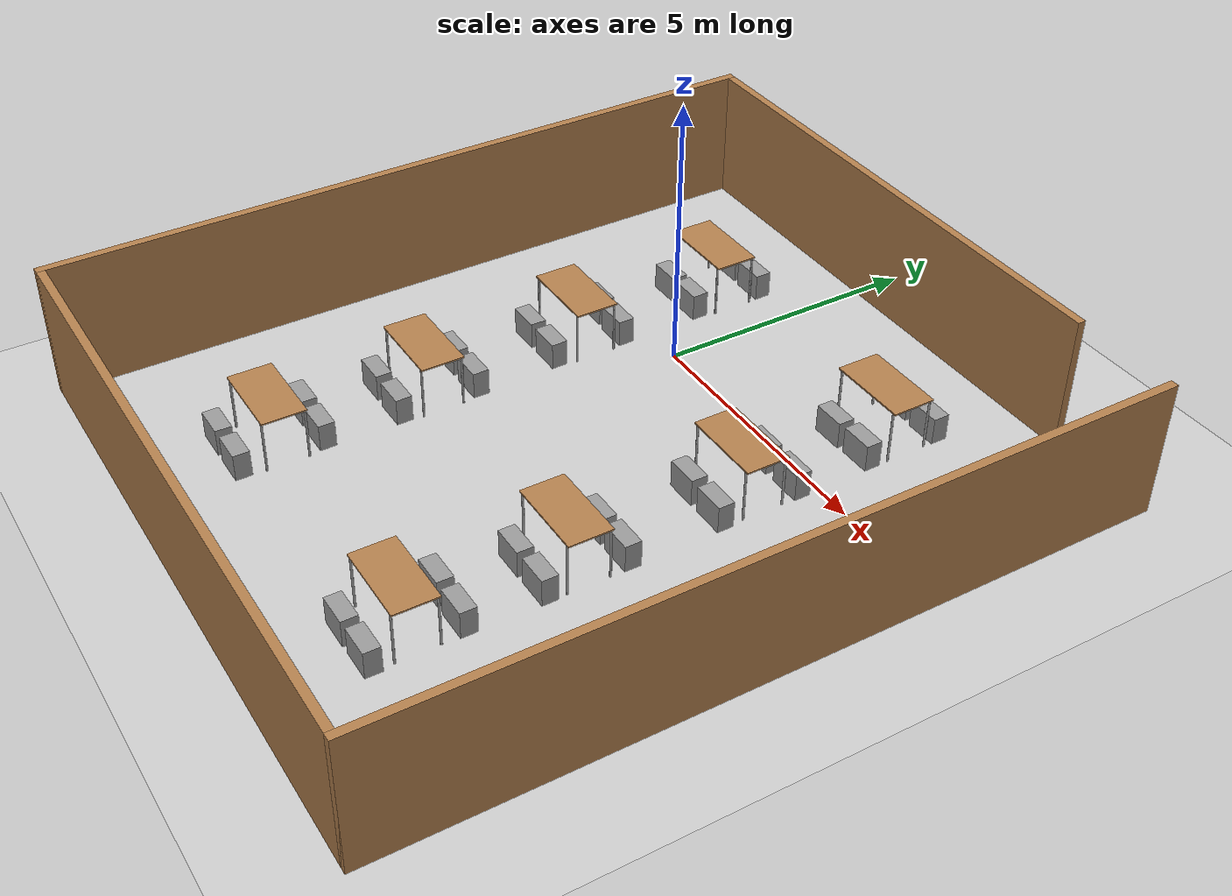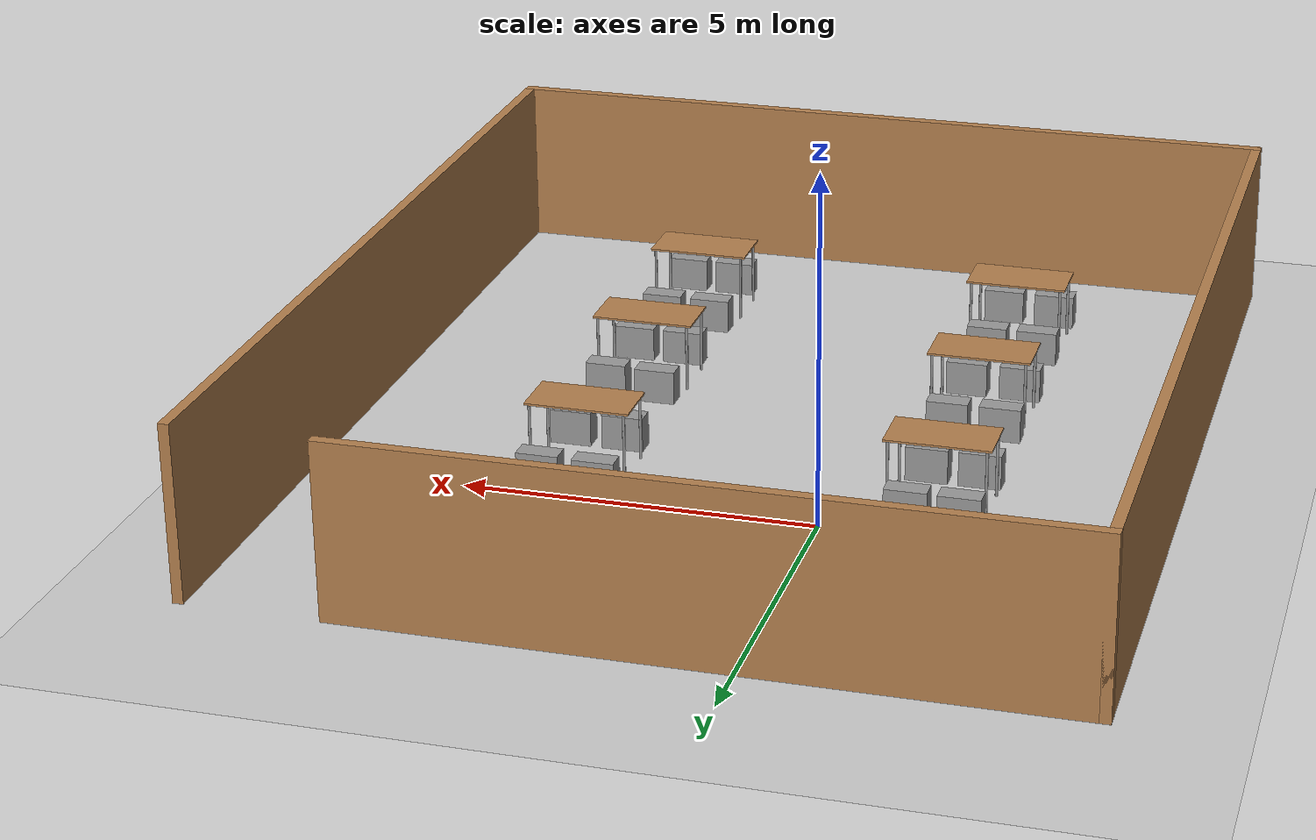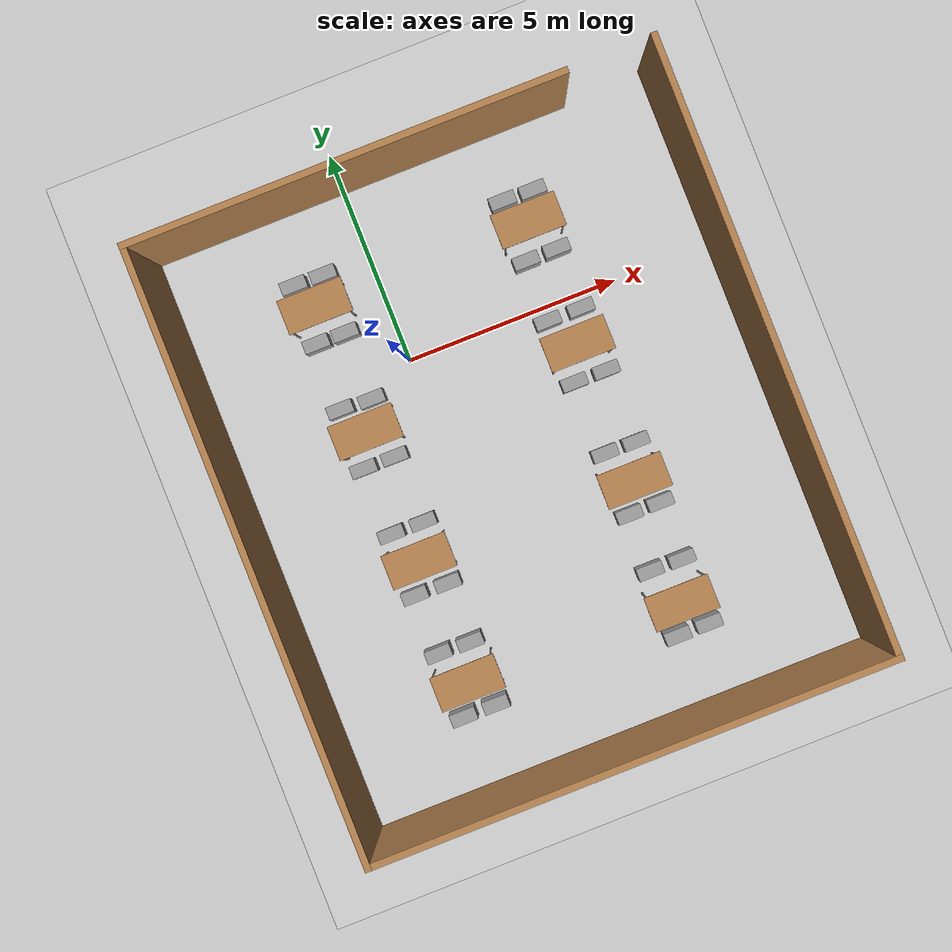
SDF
<sdf version="1.7">
 <world name="default">
  <light name="sun" type="directional">
   <pose>0 0 10 0 -0 0</pose>
   <diffuse>0.8 0.8 0.8 1</diffuse>
   <specular>0.2 0.2 0.2 1</specular>
   <attenuation>
    <range>1000</range>
    <constant>0.9</constant>
    <linear>0.01</linear>
    <quadratic>0.001</quadratic>
   </attenuation>
   <direction>-0.5 0.1 -0.9</direction>
   <spot><inner_angle>0</inner_angle><outer_angle>0</outer_angle><falloff>0</falloff></spot>
  </light>
  <model name="ground_plane">
   <static>1</static>
   <link name="link">
    <collision name="collision">
     <geometry><plane><normal>0 0 1</normal><size>100 100</size></plane></geometry>
     <surface><friction><ode><mu>100</mu><mu2>50</mu2></ode></friction></surface>
    </collision>
    <visual name="visual">
     <cast_shadows>0</cast_shadows>
     <geometry><plane><normal>0 0 1</normal><size>100 100</size></plane></geometry>
     <material>
      <script><uri>file://media/materials/scripts/gazebo.material</uri><name>Gazebo/Grey</name></script>
     </material>
    </visual>
   </link>
  </model>
  <gravity>0 0 -9.8</gravity>
  <magnetic_field>6e-06 2.3e-05 -4.2e-05</magnetic_field>
  <atmosphere type="adiabatic"/>
  <physics type="ode">
   <max_step_size>0.001</max_step_size>
   <real_time_factor>1</real_time_factor>
   <real_time_update_rate>1000</real_time_update_rate>
  </physics>
  <scene><ambient>0.4 0.4 0.4 1</ambient><background>0.7 0.7 0.7 1</background><shadows>1</shadows></scene>
  <audio><device>default</device></audio>
  <spherical_coordinates>
   <surface_model>EARTH_WGS84</surface_model>
   <latitude_deg>0</latitude_deg>
   <longitude_deg>0</longitude_deg>
   <elevation>0</elevation>
   <heading_deg>0</heading_deg>
  </spherical_coordinates>
  <model name="restaurent_walls">
   <pose>1.37943 -2.77335 0 0 -0 0</pose>
   <link name="Wall_2">
    <collision name="Wall_2_Collision">
     <geometry><box><size>10 0.15 2.5</size></box></geometry>
     <pose>0 0 1.25 0 -0 0</pose>
    </collision>
    <visual name="Wall_2_Visual">
     <pose>0 0 1.25 0 -0 0</pose>
     <geometry><box><size>10 0.15 2.5</size></box></geometry>
     <material>
      <script><uri>file://media/materials/scripts/gazebo.material</uri><name>Gazebo/Wood</name></script>
      <ambient>1 1 1 1</ambient>
     </material>
     <meta><layer>0</layer></meta>
    </visual>
    <pose>-1 6.925 0 0 -0 0</pose>
   </link>
   <link name="Wall_4">
    <collision name="Wall_4_Collision">
     <geometry><box><size>14 0.15 2.5</size></box></geometry>
     <pose>0 0 1.25 0 -0 0</pose>
    </collision>
    <visual name="Wall_4_Visual">
     <pose>0 0 1.25 0 -0 0</pose>
     <geometry><box><size>14 0.15 2.5</size></box></geometry>
     <material>
      <script><uri>file://media/materials/scripts/gazebo.material</uri><name>Gazebo/Wood</name></script>
      <ambient>1 1 1 1</ambient>
     </material>
     <meta><layer>0</layer></meta>
    </visual>
    <pose>-5.925 -0 0 0 -0 -1.5708</pose>
   </link>
   <link name="Wall_5">
    <collision name="Wall_5_Collision">
     <geometry><box><size>12 0.15 2.5</size></box></geometry>
     <pose>0 0 1.25 0 -0 0</pose>
    </collision>
    <visual name="Wall_5_Visual">
     <pose>0 0 1.25 0 -0 0</pose>
     <geometry><box><size>12 0.15 2.5</size></box></geometry>
     <material>
      <script><uri>file://media/materials/scripts/gazebo.material</uri><name>Gazebo/Wood</name></script>
      <ambient>1 1 1 1</ambient>
     </material>
     <meta><layer>0</layer></meta>
    </visual>
    <pose>-0 -6.925 0 0 -0 0</pose>
   </link>
   <link name="Wall_6">
    <collision name="Wall_6_Collision">
     <geometry><box><size>14 0.15 2.5</size></box></geometry>
     <pose>0 0 1.25 0 -0 0</pose>
    </collision>
    <visual name="Wall_6_Visual">
     <pose>0 0 1.25 0 -0 0</pose>
     <geometry><box><size>14 0.15 2.5</size></box></geometry>
     <material>
      <script><uri>file://media/materials/scripts/gazebo.material</uri><name>Gazebo/Wood</name></script>
      <ambient>1 1 1 1</ambient>
     </material>
     <meta><layer>0</layer></meta>
    </visual>
    <pose>5.925 -0 0 0 -0 1.5708</pose>
   </link>
   <static>1</static>
  </model>
  <model name="table">
   <static>1</static>
   <link name="link">
    <collision name="surface">
     <pose>0 0 1 0 -0 0</pose>
     <geometry><box><size>1.5 0.8 0.03</size></box></geometry>
     <surface><friction><ode><mu>0.6</mu><mu2>0.6</mu2></ode></friction></surface>
    </collision>
    <visual name="visual1">
     <pose>0 0 1 0 -0 0</pose>
     <geometry><box><size>1.5 0.8 0.03</size></box></geometry>
     <material>
      <script><uri>file://media/materials/scripts/gazebo.material</uri><name>Gazebo/Wood</name></script>
     </material>
    </visual>
    <collision name="front_left_leg">
     <pose>0.68 0.38 0.5 0 -0 0</pose>
     <geometry><cylinder><radius>0.02</radius><length>1</length></cylinder></geometry>
    </collision>
    <visual name="front_left_leg">
     <pose>0.68 0.38 0.5 0 -0 0</pose>
     <geometry><cylinder><radius>0.02</radius><length>1</length></cylinder></geometry>
     <material>
      <script><uri>file://media/materials/scripts/gazebo.material</uri><name>Gazebo/Grey</name></script>
     </material>
    </visual>
    <collision name="front_right_leg">
     <pose>0.68 -0.38 0.5 0 -0 0</pose>
     <geometry><cylinder><radius>0.02</radius><length>1</length></cylinder></geometry>
    </collision>
    <visual name="front_right_leg">
     <pose>0.68 -0.38 0.5 0 -0 0</pose>
     <geometry><cylinder><radius>0.02</radius><length>1</length></cylinder></geometry>
     <material>
      <script><uri>file://media/materials/scripts/gazebo.material</uri><name>Gazebo/Grey</name></script>
     </material>
    </visual>
    <collision name="back_right_leg">
     <pose>-0.68 -0.38 0.5 0 -0 0</pose>
     <geometry><cylinder><radius>0.02</radius><length>1</length></cylinder></geometry>
    </collision>
    <visual name="back_right_leg">
     <pose>-0.68 -0.38 0.5 0 -0 0</pose>
     <geometry><cylinder><radius>0.02</radius><length>1</length></cylinder></geometry>
     <material>
      <script><uri>file://media/materials/scripts/gazebo.material</uri><name>Gazebo/Grey</name></script>
     </material>
    </visual>
    <collision name="back_left_leg">
     <pose>-0.68 0.38 0.5 0 -0 0</pose>
     <geometry><cylinder><radius>0.02</radius><length>1</length></cylinder></geometry>
    </collision>
    <visual name="back_left_leg">
     <pose>-0.68 0.38 0.5 0 -0 0</pose>
     <geometry><cylinder><radius>0.02</radius><length>1</length></cylinder></geometry>
     <material>
      <script><uri>file://media/materials/scripts/gazebo.material</uri><name>Gazebo/Grey</name></script>
     </material>
    </visual>
   </link>
   <pose>-1.44943 1.78646 0 0 -0 0</pose>
  </model>
  <model name="table_0">
   <static>1</static>
   <link name="link">
    <collision name="surface">
     <pose>0 0 1 0 -0 0</pose>
     <geometry><box><size>1.5 0.8 0.03</size></box></geometry>
     <surface><friction><ode><mu>0.6</mu><mu2>0.6</mu2></ode></friction></surface>
    </collision>
    <visual name="visual1">
     <pose>0 0 1 0 -0 0</pose>
     <geometry><box><size>1.5 0.8 0.03</size></box></geometry>
     <material>
      <script><uri>file://media/materials/scripts/gazebo.material</uri><name>Gazebo/Wood</name></script>
     </material>
    </visual>
    <collision name="front_left_leg">
     <pose>0.68 0.38 0.5 0 -0 0</pose>
     <geometry><cylinder><radius>0.02</radius><length>1</length></cylinder></geometry>
    </collision>
    <visual name="front_left_leg">
     <pose>0.68 0.38 0.5 0 -0 0</pose>
     <geometry><cylinder><radius>0.02</radius><length>1</length></cylinder></geometry>
     <material>
      <script><uri>file://media/materials/scripts/gazebo.material</uri><name>Gazebo/Grey</name></script>
     </material>
    </visual>
    <collision name="front_right_leg">
     <pose>0.68 -0.38 0.5 0 -0 0</pose>
     <geometry><cylinder><radius>0.02</radius><length>1</length></cylinder></geometry>
    </collision>
    <visual name="front_right_leg">
     <pose>0.68 -0.38 0.5 0 -0 0</pose>
     <geometry><cylinder><radius>0.02</radius><length>1</length></cylinder></geometry>
     <material>
      <script><uri>file://media/materials/scripts/gazebo.material</uri><name>Gazebo/Grey</name></script>
     </material>
    </visual>
    <collision name="back_right_leg">
     <pose>-0.68 -0.38 0.5 0 -0 0</pose>
     <geometry><cylinder><radius>0.02</radius><length>1</length></cylinder></geometry>
    </collision>
    <visual name="back_right_leg">
     <pose>-0.68 -0.38 0.5 0 -0 0</pose>
     <geometry><cylinder><radius>0.02</radius><length>1</length></cylinder></geometry>
     <material>
      <script><uri>file://media/materials/scripts/gazebo.material</uri><name>Gazebo/Grey</name></script>
     </material>
    </visual>
    <collision name="back_left_leg">
     <pose>-0.68 0.38 0.5 0 -0 0</pose>
     <geometry><cylinder><radius>0.02</radius><length>1</length></cylinder></geometry>
    </collision>
    <visual name="back_left_leg">
     <pose>-0.68 0.38 0.5 0 -0 0</pose>
     <geometry><cylinder><radius>0.02</radius><length>1</length></cylinder></geometry>
     <material>
      <script><uri>file://media/materials/scripts/gazebo.material</uri><name>Gazebo/Grey</name></script>
     </material>
    </visual>
   </link>
   <pose>-1.43197 -1.18837 0 0 -0 0</pose>
  </model>
  <model name="table_1">
   <static>1</static>
   <link name="link">
    <collision name="surface">
     <pose>0 0 1 0 -0 0</pose>
     <geometry><box><size>1.5 0.8 0.03</size></box></geometry>
     <surface><friction><ode><mu>0.6</mu><mu2>0.6</mu2></ode></friction></surface>
    </collision>
    <visual name="visual1">
     <pose>0 0 1 0 -0 0</pose>
     <geometry><box><size>1.5 0.8 0.03</size></box></geometry>
     <material>
      <script><uri>file://media/materials/scripts/gazebo.material</uri><name>Gazebo/Wood</name></script>
     </material>
    </visual>
    <collision name="front_left_leg">
     <pose>0.68 0.38 0.5 0 -0 0</pose>
     <geometry><cylinder><radius>0.02</radius><length>1</length></cylinder></geometry>
    </collision>
    <visual name="front_left_leg">
     <pose>0.68 0.38 0.5 0 -0 0</pose>
     <geometry><cylinder><radius>0.02</radius><length>1</length></cylinder></geometry>
     <material>
      <script><uri>file://media/materials/scripts/gazebo.material</uri><name>Gazebo/Grey</name></script>
     </material>
    </visual>
    <collision name="front_right_leg">
     <pose>0.68 -0.38 0.5 0 -0 0</pose>
     <geometry><cylinder><radius>0.02</radius><length>1</length></cylinder></geometry>
    </collision>
    <visual name="front_right_leg">
     <pose>0.68 -0.38 0.5 0 -0 0</pose>
     <geometry><cylinder><radius>0.02</radius><length>1</length></cylinder></geometry>
     <material>
      <script><uri>file://media/materials/scripts/gazebo.material</uri><name>Gazebo/Grey</name></script>
     </material>
    </visual>
    <collision name="back_right_leg">
     <pose>-0.68 -0.38 0.5 0 -0 0</pose>
     <geometry><cylinder><radius>0.02</radius><length>1</length></cylinder></geometry>
    </collision>
    <visual name="back_right_leg">
     <pose>-0.68 -0.38 0.5 0 -0 0</pose>
     <geometry><cylinder><radius>0.02</radius><length>1</length></cylinder></geometry>
     <material>
      <script><uri>file://media/materials/scripts/gazebo.material</uri><name>Gazebo/Grey</name></script>
     </material>
    </visual>
    <collision name="back_left_leg">
     <pose>-0.68 0.38 0.5 0 -0 0</pose>
     <geometry><cylinder><radius>0.02</radius><length>1</length></cylinder></geometry>
    </collision>
    <visual name="back_left_leg">
     <pose>-0.68 0.38 0.5 0 -0 0</pose>
     <geometry><cylinder><radius>0.02</radius><length>1</length></cylinder></geometry>
     <material>
      <script><uri>file://media/materials/scripts/gazebo.material</uri><name>Gazebo/Grey</name></script>
     </material>
    </visual>
   </link>
   <pose>-1.37961 -4.25534 0 0 -0 0</pose>
  </model>
  <model name="table_2">
   <static>1</static>
   <link name="link">
    <collision name="surface">
     <pose>0 0 1 0 -0 0</pose>
     <geometry><box><size>1.5 0.8 0.03</size></box></geometry>
     <surface><friction><ode><mu>0.6</mu><mu2>0.6</mu2></ode></friction></surface>
    </collision>
    <visual name="visual1">
     <pose>0 0 1 0 -0 0</pose>
     <geometry><box><size>1.5 0.8 0.03</size></box></geometry>
     <material>
      <script><uri>file://media/materials/scripts/gazebo.material</uri><name>Gazebo/Wood</name></script>
     </material>
    </visual>
    <collision name="front_left_leg">
     <pose>0.68 0.38 0.5 0 -0 0</pose>
     <geometry><cylinder><radius>0.02</radius><length>1</length></cylinder></geometry>
    </collision>
    <visual name="front_left_leg">
     <pose>0.68 0.38 0.5 0 -0 0</pose>
     <geometry><cylinder><radius>0.02</radius><length>1</length></cylinder></geometry>
     <material>
      <script><uri>file://media/materials/scripts/gazebo.material</uri><name>Gazebo/Grey</name></script>
     </material>
    </visual>
    <collision name="front_right_leg">
     <pose>0.68 -0.38 0.5 0 -0 0</pose>
     <geometry><cylinder><radius>0.02</radius><length>1</length></cylinder></geometry>
    </collision>
    <visual name="front_right_leg">
     <pose>0.68 -0.38 0.5 0 -0 0</pose>
     <geometry><cylinder><radius>0.02</radius><length>1</length></cylinder></geometry>
     <material>
      <script><uri>file://media/materials/scripts/gazebo.material</uri><name>Gazebo/Grey</name></script>
     </material>
    </visual>
    <collision name="back_right_leg">
     <pose>-0.68 -0.38 0.5 0 -0 0</pose>
     <geometry><cylinder><radius>0.02</radius><length>1</length></cylinder></geometry>
    </collision>
    <visual name="back_right_leg">
     <pose>-0.68 -0.38 0.5 0 -0 0</pose>
     <geometry><cylinder><radius>0.02</radius><length>1</length></cylinder></geometry>
     <material>
      <script><uri>file://media/materials/scripts/gazebo.material</uri><name>Gazebo/Grey</name></script>
     </material>
    </visual>
    <collision name="back_left_leg">
     <pose>-0.68 0.38 0.5 0 -0 0</pose>
     <geometry><cylinder><radius>0.02</radius><length>1</length></cylinder></geometry>
    </collision>
    <visual name="back_left_leg">
     <pose>-0.68 0.38 0.5 0 -0 0</pose>
     <geometry><cylinder><radius>0.02</radius><length>1</length></cylinder></geometry>
     <material>
      <script><uri>file://media/materials/scripts/gazebo.material</uri><name>Gazebo/Grey</name></script>
     </material>
    </visual>
   </link>
   <pose>-1.36569 -7.13557 0 0 -0 0</pose>
  </model>
  <model name="table_3">
   <static>1</static>
   <link name="link">
    <collision name="surface">
     <pose>0 0 1 0 -0 0</pose>
     <geometry><box><size>1.5 0.8 0.03</size></box></geometry>
     <surface><friction><ode><mu>0.6</mu><mu2>0.6</mu2></ode></friction></surface>
    </collision>
    <visual name="visual1">
     <pose>0 0 1 0 -0 0</pose>
     <geometry><box><size>1.5 0.8 0.03</size></box></geometry>
     <material>
      <script><uri>file://media/materials/scripts/gazebo.material</uri><name>Gazebo/Wood</name></script>
     </material>
    </visual>
    <collision name="front_left_leg">
     <pose>0.68 0.38 0.5 0 -0 0</pose>
     <geometry><cylinder><radius>0.02</radius><length>1</length></cylinder></geometry>
    </collision>
    <visual name="front_left_leg">
     <pose>0.68 0.38 0.5 0 -0 0</pose>
     <geometry><cylinder><radius>0.02</radius><length>1</length></cylinder></geometry>
     <material>
      <script><uri>file://media/materials/scripts/gazebo.material</uri><name>Gazebo/Grey</name></script>
     </material>
    </visual>
    <collision name="front_right_leg">
     <pose>0.68 -0.38 0.5 0 -0 0</pose>
     <geometry><cylinder><radius>0.02</radius><length>1</length></cylinder></geometry>
    </collision>
    <visual name="front_right_leg">
     <pose>0.68 -0.38 0.5 0 -0 0</pose>
     <geometry><cylinder><radius>0.02</radius><length>1</length></cylinder></geometry>
     <material>
      <script><uri>file://media/materials/scripts/gazebo.material</uri><name>Gazebo/Grey</name></script>
     </material>
    </visual>
    <collision name="back_right_leg">
     <pose>-0.68 -0.38 0.5 0 -0 0</pose>
     <geometry><cylinder><radius>0.02</radius><length>1</length></cylinder></geometry>
    </collision>
    <visual name="back_right_leg">
     <pose>-0.68 -0.38 0.5 0 -0 0</pose>
     <geometry><cylinder><radius>0.02</radius><length>1</length></cylinder></geometry>
     <material>
      <script><uri>file://media/materials/scripts/gazebo.material</uri><name>Gazebo/Grey</name></script>
     </material>
    </visual>
    <collision name="back_left_leg">
     <pose>-0.68 0.38 0.5 0 -0 0</pose>
     <geometry><cylinder><radius>0.02</radius><length>1</length></cylinder></geometry>
    </collision>
    <visual name="back_left_leg">
     <pose>-0.68 0.38 0.5 0 -0 0</pose>
     <geometry><cylinder><radius>0.02</radius><length>1</length></cylinder></geometry>
     <material>
      <script><uri>file://media/materials/scripts/gazebo.material</uri><name>Gazebo/Grey</name></script>
     </material>
    </visual>
   </link>
   <pose>3.59201 1.81848 0 0 -0 0</pose>
  </model>
  <model name="table_4">
   <static>1</static>
   <link name="link">
    <collision name="surface">
     <pose>0 0 1 0 -0 0</pose>
     <geometry><box><size>1.5 0.8 0.03</size></box></geometry>
     <surface><friction><ode><mu>0.6</mu><mu2>0.6</mu2></ode></friction></surface>
    </collision>
    <visual name="visual1">
     <pose>0 0 1 0 -0 0</pose>
     <geometry><box><size>1.5 0.8 0.03</size></box></geometry>
     <material>
      <script><uri>file://media/materials/scripts/gazebo.material</uri><name>Gazebo/Wood</name></script>
     </material>
    </visual>
    <collision name="front_left_leg">
     <pose>0.68 0.38 0.5 0 -0 0</pose>
     <geometry><cylinder><radius>0.02</radius><length>1</length></cylinder></geometry>
    </collision>
    <visual name="front_left_leg">
     <pose>0.68 0.38 0.5 0 -0 0</pose>
     <geometry><cylinder><radius>0.02</radius><length>1</length></cylinder></geometry>
     <material>
      <script><uri>file://media/materials/scripts/gazebo.material</uri><name>Gazebo/Grey</name></script>
     </material>
    </visual>
    <collision name="front_right_leg">
     <pose>0.68 -0.38 0.5 0 -0 0</pose>
     <geometry><cylinder><radius>0.02</radius><length>1</length></cylinder></geometry>
    </collision>
    <visual name="front_right_leg">
     <pose>0.68 -0.38 0.5 0 -0 0</pose>
     <geometry><cylinder><radius>0.02</radius><length>1</length></cylinder></geometry>
     <material>
      <script><uri>file://media/materials/scripts/gazebo.material</uri><name>Gazebo/Grey</name></script>
     </material>
    </visual>
    <collision name="back_right_leg">
     <pose>-0.68 -0.38 0.5 0 -0 0</pose>
     <geometry><cylinder><radius>0.02</radius><length>1</length></cylinder></geometry>
    </collision>
    <visual name="back_right_leg">
     <pose>-0.68 -0.38 0.5 0 -0 0</pose>
     <geometry><cylinder><radius>0.02</radius><length>1</length></cylinder></geometry>
     <material>
      <script><uri>file://media/materials/scripts/gazebo.material</uri><name>Gazebo/Grey</name></script>
     </material>
    </visual>
    <collision name="back_left_leg">
     <pose>-0.68 0.38 0.5 0 -0 0</pose>
     <geometry><cylinder><radius>0.02</radius><length>1</length></cylinder></geometry>
    </collision>
    <visual name="back_left_leg">
     <pose>-0.68 0.38 0.5 0 -0 0</pose>
     <geometry><cylinder><radius>0.02</radius><length>1</length></cylinder></geometry>
     <material>
      <script><uri>file://media/materials/scripts/gazebo.material</uri><name>Gazebo/Grey</name></script>
     </material>
    </visual>
   </link>
   <pose>3.60676 -1.09378 0 0 -0 0</pose>
  </model>
  <model name="table_5">
   <static>1</static>
   <link name="link">
    <collision name="surface">
     <pose>0 0 1 0 -0 0</pose>
     <geometry><box><size>1.5 0.8 0.03</size></box></geometry>
     <surface><friction><ode><mu>0.6</mu><mu2>0.6</mu2></ode></friction></surface>
    </collision>
    <visual name="visual1">
     <pose>0 0 1 0 -0 0</pose>
     <geometry><box><size>1.5 0.8 0.03</size></box></geometry>
     <material>
      <script><uri>file://media/materials/scripts/gazebo.material</uri><name>Gazebo/Wood</name></script>
     </material>
    </visual>
    <collision name="front_left_leg">
     <pose>0.68 0.38 0.5 0 -0 0</pose>
     <geometry><cylinder><radius>0.02</radius><length>1</length></cylinder></geometry>
    </collision>
    <visual name="front_left_leg">
     <pose>0.68 0.38 0.5 0 -0 0</pose>
     <geometry><cylinder><radius>0.02</radius><length>1</length></cylinder></geometry>
     <material>
      <script><uri>file://media/materials/scripts/gazebo.material</uri><name>Gazebo/Grey</name></script>
     </material>
    </visual>
    <collision name="front_right_leg">
     <pose>0.68 -0.38 0.5 0 -0 0</pose>
     <geometry><cylinder><radius>0.02</radius><length>1</length></cylinder></geometry>
    </collision>
    <visual name="front_right_leg">
     <pose>0.68 -0.38 0.5 0 -0 0</pose>
     <geometry><cylinder><radius>0.02</radius><length>1</length></cylinder></geometry>
     <material>
      <script><uri>file://media/materials/scripts/gazebo.material</uri><name>Gazebo/Grey</name></script>
     </material>
    </visual>
    <collision name="back_right_leg">
     <pose>-0.68 -0.38 0.5 0 -0 0</pose>
     <geometry><cylinder><radius>0.02</radius><length>1</length></cylinder></geometry>
    </collision>
    <visual name="back_right_leg">
     <pose>-0.68 -0.38 0.5 0 -0 0</pose>
     <geometry><cylinder><radius>0.02</radius><length>1</length></cylinder></geometry>
     <material>
      <script><uri>file://media/materials/scripts/gazebo.material</uri><name>Gazebo/Grey</name></script>
     </material>
    </visual>
    <collision name="back_left_leg">
     <pose>-0.68 0.38 0.5 0 -0 0</pose>
     <geometry><cylinder><radius>0.02</radius><length>1</length></cylinder></geometry>
    </collision>
    <visual name="back_left_leg">
     <pose>-0.68 0.38 0.5 0 -0 0</pose>
     <geometry><cylinder><radius>0.02</radius><length>1</length></cylinder></geometry>
     <material>
      <script><uri>file://media/materials/scripts/gazebo.material</uri><name>Gazebo/Grey</name></script>
     </material>
    </visual>
   </link>
   <pose>3.66552 -4.34774 0 0 -0 0</pose>
  </model>
  <model name="table_6">
   <static>1</static>
   <link name="link">
    <collision name="surface">
     <pose>0 0 1 0 -0 0</pose>
     <geometry><box><size>1.5 0.8 0.03</size></box></geometry>
     <surface><friction><ode><mu>0.6</mu><mu2>0.6</mu2></ode></friction></surface>
    </collision>
    <visual name="visual1">
     <pose>0 0 1 0 -0 0</pose>
     <geometry><box><size>1.5 0.8 0.03</size></box></geometry>
     <material>
      <script><uri>file://media/materials/scripts/gazebo.material</uri><name>Gazebo/Wood</name></script>
     </material>
    </visual>
    <collision name="front_left_leg">
     <pose>0.68 0.38 0.5 0 -0 0</pose>
     <geometry><cylinder><radius>0.02</radius><length>1</length></cylinder></geometry>
    </collision>
    <visual name="front_left_leg">
     <pose>0.68 0.38 0.5 0 -0 0</pose>
     <geometry><cylinder><radius>0.02</radius><length>1</length></cylinder></geometry>
     <material>
      <script><uri>file://media/materials/scripts/gazebo.material</uri><name>Gazebo/Grey</name></script>
     </material>
    </visual>
    <collision name="front_right_leg">
     <pose>0.68 -0.38 0.5 0 -0 0</pose>
     <geometry><cylinder><radius>0.02</radius><length>1</length></cylinder></geometry>
    </collision>
    <visual name="front_right_leg">
     <pose>0.68 -0.38 0.5 0 -0 0</pose>
     <geometry><cylinder><radius>0.02</radius><length>1</length></cylinder></geometry>
     <material>
      <script><uri>file://media/materials/scripts/gazebo.material</uri><name>Gazebo/Grey</name></script>
     </material>
    </visual>
    <collision name="back_right_leg">
     <pose>-0.68 -0.38 0.5 0 -0 0</pose>
     <geometry><cylinder><radius>0.02</radius><length>1</length></cylinder></geometry>
    </collision>
    <visual name="back_right_leg">
     <pose>-0.68 -0.38 0.5 0 -0 0</pose>
     <geometry><cylinder><radius>0.02</radius><length>1</length></cylinder></geometry>
     <material>
      <script><uri>file://media/materials/scripts/gazebo.material</uri><name>Gazebo/Grey</name></script>
     </material>
    </visual>
    <collision name="back_left_leg">
     <pose>-0.68 0.38 0.5 0 -0 0</pose>
     <geometry><cylinder><radius>0.02</radius><length>1</length></cylinder></geometry>
    </collision>
    <visual name="back_left_leg">
     <pose>-0.68 0.38 0.5 0 -0 0</pose>
     <geometry><cylinder><radius>0.02</radius><length>1</length></cylinder></geometry>
     <material>
      <script><uri>file://media/materials/scripts/gazebo.material</uri><name>Gazebo/Grey</name></script>
     </material>
    </visual>
   </link>
   <pose>3.64793 -7.22796 0 0 -0 0</pose>
  </model>
  <model name="chair">
   <link name="link">
    <inertial>
     <mass>1</mass>
     <inertia>
      <ixx>0.166667</ixx>
      <ixy>0</ixy>
      <ixz>0</ixz>
      <iyy>0.166667</iyy>
      <iyz>0</iyz>
      <izz>0.166667</izz>
     </inertia>
    </inertial>
    <visual name="visual">
     <geometry><box><size>0.6 0.3 0.5</size></box></geometry>
     <material>
      <script><name>Gazebo/Grey</name><uri>file://media/materials/scripts/gazebo.material</uri></script>
      <shader type="pixel"><normal_map>__default__</normal_map></shader>
      <ambient>0.3 0.3 0.3 1</ambient>
      <diffuse>0.7 0.7 0.7 1</diffuse>
      <specular>0.01 0.01 0.01 1</specular>
      <emissive>0.2 0.6 0 1</emissive>
     </material>
    </visual>
    <collision name="collision">
     <geometry><box><size>0.6 0.3 0.5</size></box></geometry>
     <surface>
      <friction>
       <ode><mu>1</mu><mu2>1</mu2><fdir1>0 0 0</fdir1><slip1>0</slip1><slip2>0</slip2></ode>
       <torsional>
        <coefficient>1</coefficient>
        <patch_radius>0</patch_radius>
        <surface_radius>0</surface_radius>
        <use_patch_radius>1</use_patch_radius>
        <ode><slip>0</slip></ode>
       </torsional>
      </friction>
      <bounce><restitution_coefficient>0</restitution_coefficient><threshold>1e+06</threshold></bounce>
      <contact>
       <collide_without_contact>0</collide_without_contact>
       <collide_without_contact_bitmask>1</collide_without_contact_bitmask>
       <collide_bitmask>1</collide_bitmask>
       <ode>
        <soft_cfm>0</soft_cfm>
        <soft_erp>0.2</soft_erp>
        <kp>1e+13</kp>
        <kd>1</kd>
        <max_vel>0.01</max_vel>
        <min_depth>0</min_depth>
       </ode>
       <bullet>
        <split_impulse>1</split_impulse>
        <split_impulse_penetration_threshold>-0.01</split_impulse_penetration_threshold>
        <soft_cfm>0</soft_cfm>
        <soft_erp>0.2</soft_erp>
        <kp>1e+13</kp>
        <kd>1</kd>
       </bullet>
      </contact>
     </surface>
    </collision>
   </link>
   <static>0</static>
   <pose>4.06254 -6.4022 0.241541 0 -0 0</pose>
  </model>
  <model name="chair_clone_2">
   <link name="link">
    <inertial>
     <mass>1</mass>
     <inertia>
      <ixx>0.166667</ixx>
      <ixy>0</ixy>
      <ixz>0</ixz>
      <iyy>0.166667</iyy>
      <iyz>0</iyz>
      <izz>0.166667</izz>
     </inertia>
    </inertial>
    <visual name="visual">
     <geometry><box><size>0.6 0.3 0.5</size></box></geometry>
     <material>
      <script><name>Gazebo/Grey</name><uri>file://media/materials/scripts/gazebo.material</uri></script>
      <shader type="pixel"><normal_map>__default__</normal_map></shader>
      <ambient>0.3 0.3 0.3 1</ambient>
      <diffuse>0.7 0.7 0.7 1</diffuse>
      <specular>0.01 0.01 0.01 1</specular>
      <emissive>0.2 0.6 0 1</emissive>
     </material>
    </visual>
    <collision name="collision">
     <geometry><box><size>0.6 0.3 0.5</size></box></geometry>
     <surface>
      <friction>
       <ode><mu>1</mu><mu2>1</mu2><fdir1>0 0 0</fdir1><slip1>0</slip1><slip2>0</slip2></ode>
       <torsional>
        <coefficient>1</coefficient>
        <patch_radius>0</patch_radius>
        <surface_radius>0</surface_radius>
        <use_patch_radius>1</use_patch_radius>
        <ode><slip>0</slip></ode>
       </torsional>
      </friction>
      <bounce><restitution_coefficient>0</restitution_coefficient><threshold>1e+06</threshold></bounce>
      <contact>
       <collide_without_contact>0</collide_without_contact>
       <collide_without_contact_bitmask>1</collide_without_contact_bitmask>
       <collide_bitmask>1</collide_bitmask>
       <ode>
        <soft_cfm>0</soft_cfm>
        <soft_erp>0.2</soft_erp>
        <kp>1e+13</kp>
        <kd>1</kd>
        <max_vel>0.01</max_vel>
        <min_depth>0</min_depth>
       </ode>
       <bullet>
        <split_impulse>1</split_impulse>
        <split_impulse_penetration_threshold>-0.01</split_impulse_penetration_threshold>
        <soft_cfm>0</soft_cfm>
        <soft_erp>0.2</soft_erp>
        <kp>1e+13</kp>
        <kd>1</kd>
       </bullet>
      </contact>
     </surface>
    </collision>
   </link>
   <static>0</static>
   <pose>-1.03447 -6.39345 0.242909 0 -0 0</pose>
  </model>
  <model name="chair_clone">
   <link name="link">
    <inertial>
     <mass>1</mass>
     <inertia>
      <ixx>0.166667</ixx>
      <ixy>0</ixy>
      <ixz>0</ixz>
      <iyy>0.166667</iyy>
      <iyz>0</iyz>
      <izz>0.166667</izz>
     </inertia>
    </inertial>
    <visual name="visual">
     <geometry><box><size>0.6 0.3 0.5</size></box></geometry>
     <material>
      <script><name>Gazebo/Grey</name><uri>file://media/materials/scripts/gazebo.material</uri></script>
      <shader type="pixel"><normal_map>__default__</normal_map></shader>
      <ambient>0.3 0.3 0.3 1</ambient>
      <diffuse>0.7 0.7 0.7 1</diffuse>
      <specular>0.01 0.01 0.01 1</specular>
      <emissive>0.2 0.6 0 1</emissive>
     </material>
    </visual>
    <collision name="collision">
     <geometry><box><size>0.6 0.3 0.5</size></box></geometry>
     <surface>
      <friction>
       <ode><mu>1</mu><mu2>1</mu2><fdir1>0 0 0</fdir1><slip1>0</slip1><slip2>0</slip2></ode>
       <torsional>
        <coefficient>1</coefficient>
        <patch_radius>0</patch_radius>
        <surface_radius>0</surface_radius>
        <use_patch_radius>1</use_patch_radius>
        <ode><slip>0</slip></ode>
       </torsional>
      </friction>
      <bounce><restitution_coefficient>0</restitution_coefficient><threshold>1e+06</threshold></bounce>
      <contact>
       <collide_without_contact>0</collide_without_contact>
       <collide_without_contact_bitmask>1</collide_without_contact_bitmask>
       <collide_bitmask>1</collide_bitmask>
       <ode>
        <soft_cfm>0</soft_cfm>
        <soft_erp>0.2</soft_erp>
        <kp>1e+13</kp>
        <kd>1</kd>
        <max_vel>0.01</max_vel>
        <min_depth>0</min_depth>
       </ode>
       <bullet>
        <split_impulse>1</split_impulse>
        <split_impulse_penetration_threshold>-0.01</split_impulse_penetration_threshold>
        <soft_cfm>0</soft_cfm>
        <soft_erp>0.2</soft_erp>
        <kp>1e+13</kp>
        <kd>1</kd>
       </bullet>
      </contact>
     </surface>
    </collision>
   </link>
   <static>0</static>
   <pose>3.30174 -6.39577 0.238371 0 -0 0</pose>
  </model>
  <model name="chair_clone_0">
   <link name="link">
    <inertial>
     <mass>1</mass>
     <inertia>
      <ixx>0.166667</ixx>
      <ixy>0</ixy>
      <ixz>0</ixz>
      <iyy>0.166667</iyy>
      <iyz>0</iyz>
      <izz>0.166667</izz>
     </inertia>
    </inertial>
    <visual name="visual">
     <geometry><box><size>0.6 0.3 0.5</size></box></geometry>
     <material>
      <script><name>Gazebo/Grey</name><uri>file://media/materials/scripts/gazebo.material</uri></script>
      <shader type="pixel"><normal_map>__default__</normal_map></shader>
      <ambient>0.3 0.3 0.3 1</ambient>
      <diffuse>0.7 0.7 0.7 1</diffuse>
      <specular>0.01 0.01 0.01 1</specular>
      <emissive>0.2 0.6 0 1</emissive>
     </material>
    </visual>
    <collision name="collision">
     <geometry><box><size>0.6 0.3 0.5</size></box></geometry>
     <surface>
      <friction>
       <ode><mu>1</mu><mu2>1</mu2><fdir1>0 0 0</fdir1><slip1>0</slip1><slip2>0</slip2></ode>
       <torsional>
        <coefficient>1</coefficient>
        <patch_radius>0</patch_radius>
        <surface_radius>0</surface_radius>
        <use_patch_radius>1</use_patch_radius>
        <ode><slip>0</slip></ode>
       </torsional>
      </friction>
      <bounce><restitution_coefficient>0</restitution_coefficient><threshold>1e+06</threshold></bounce>
      <contact>
       <collide_without_contact>0</collide_without_contact>
       <collide_without_contact_bitmask>1</collide_without_contact_bitmask>
       <collide_bitmask>1</collide_bitmask>
       <ode>
        <soft_cfm>0</soft_cfm>
        <soft_erp>0.2</soft_erp>
        <kp>1e+13</kp>
        <kd>1</kd>
        <max_vel>0.01</max_vel>
        <min_depth>0</min_depth>
       </ode>
       <bullet>
        <split_impulse>1</split_impulse>
        <split_impulse_penetration_threshold>-0.01</split_impulse_penetration_threshold>
        <soft_cfm>0</soft_cfm>
        <soft_erp>0.2</soft_erp>
        <kp>1e+13</kp>
        <kd>1</kd>
       </bullet>
      </contact>
     </surface>
    </collision>
   </link>
   <static>0</static>
   <pose>3.34323 -7.97211 0.245737 0 -0 0</pose>
  </model>
  <model name="chair_clone_1">
   <link name="link">
    <inertial>
     <mass>1</mass>
     <inertia>
      <ixx>0.166667</ixx>
      <ixy>0</ixy>
      <ixz>0</ixz>
      <iyy>0.166667</iyy>
      <iyz>0</iyz>
      <izz>0.166667</izz>
     </inertia>
    </inertial>
    <visual name="visual">
     <geometry><box><size>0.6 0.3 0.5</size></box></geometry>
     <material>
      <script><name>Gazebo/Grey</name><uri>file://media/materials/scripts/gazebo.material</uri></script>
      <shader type="pixel"><normal_map>__default__</normal_map></shader>
      <ambient>0.3 0.3 0.3 1</ambient>
      <diffuse>0.7 0.7 0.7 1</diffuse>
      <specular>0.01 0.01 0.01 1</specular>
      <emissive>0.2 0.6 0 1</emissive>
     </material>
    </visual>
    <collision name="collision">
     <geometry><box><size>0.6 0.3 0.5</size></box></geometry>
     <surface>
      <friction>
       <ode><mu>1</mu><mu2>1</mu2><fdir1>0 0 0</fdir1><slip1>0</slip1><slip2>0</slip2></ode>
       <torsional>
        <coefficient>1</coefficient>
        <patch_radius>0</patch_radius>
        <surface_radius>0</surface_radius>
        <use_patch_radius>1</use_patch_radius>
        <ode><slip>0</slip></ode>
       </torsional>
      </friction>
      <bounce><restitution_coefficient>0</restitution_coefficient><threshold>1e+06</threshold></bounce>
      <contact>
       <collide_without_contact>0</collide_without_contact>
       <collide_without_contact_bitmask>1</collide_without_contact_bitmask>
       <collide_bitmask>1</collide_bitmask>
       <ode>
        <soft_cfm>0</soft_cfm>
        <soft_erp>0.2</soft_erp>
        <kp>1e+13</kp>
        <kd>1</kd>
        <max_vel>0.01</max_vel>
        <min_depth>0</min_depth>
       </ode>
       <bullet>
        <split_impulse>1</split_impulse>
        <split_impulse_penetration_threshold>-0.01</split_impulse_penetration_threshold>
        <soft_cfm>0</soft_cfm>
        <soft_erp>0.2</soft_erp>
        <kp>1e+13</kp>
        <kd>1</kd>
       </bullet>
      </contact>
     </surface>
    </collision>
   </link>
   <static>0</static>
   <pose>4.09259 -7.96309 0.246409 0 -0 0</pose>
  </model>
  <model name="chair_clone_3">
   <link name="link">
    <inertial>
     <mass>1</mass>
     <inertia>
      <ixx>0.166667</ixx>
      <ixy>0</ixy>
      <ixz>0</ixz>
      <iyy>0.166667</iyy>
      <iyz>0</iyz>
      <izz>0.166667</izz>
     </inertia>
    </inertial>
    <visual name="visual">
     <geometry><box><size>0.6 0.3 0.5</size></box></geometry>
     <material>
      <script><name>Gazebo/Grey</name><uri>file://media/materials/scripts/gazebo.material</uri></script>
      <shader type="pixel"><normal_map>__default__</normal_map></shader>
      <ambient>0.3 0.3 0.3 1</ambient>
      <diffuse>0.7 0.7 0.7 1</diffuse>
      <specular>0.01 0.01 0.01 1</specular>
      <emissive>0.2 0.6 0 1</emissive>
     </material>
    </visual>
    <collision name="collision">
     <geometry><box><size>0.6 0.3 0.5</size></box></geometry>
     <surface>
      <friction>
       <ode><mu>1</mu><mu2>1</mu2><fdir1>0 0 0</fdir1><slip1>0</slip1><slip2>0</slip2></ode>
       <torsional>
        <coefficient>1</coefficient>
        <patch_radius>0</patch_radius>
        <surface_radius>0</surface_radius>
        <use_patch_radius>1</use_patch_radius>
        <ode><slip>0</slip></ode>
       </torsional>
      </friction>
      <bounce><restitution_coefficient>0</restitution_coefficient><threshold>1e+06</threshold></bounce>
      <contact>
       <collide_without_contact>0</collide_without_contact>
       <collide_without_contact_bitmask>1</collide_without_contact_bitmask>
       <collide_bitmask>1</collide_bitmask>
       <ode>
        <soft_cfm>0</soft_cfm>
        <soft_erp>0.2</soft_erp>
        <kp>1e+13</kp>
        <kd>1</kd>
        <max_vel>0.01</max_vel>
        <min_depth>0</min_depth>
       </ode>
       <bullet>
        <split_impulse>1</split_impulse>
        <split_impulse_penetration_threshold>-0.01</split_impulse_penetration_threshold>
        <soft_cfm>0</soft_cfm>
        <soft_erp>0.2</soft_erp>
        <kp>1e+13</kp>
        <kd>1</kd>
       </bullet>
      </contact>
     </surface>
    </collision>
   </link>
   <static>0</static>
   <pose>-1.01301 -7.90541 0.244469 0 -0 0</pose>
  </model>
  <model name="chair_clone_4">
   <link name="link">
    <inertial>
     <mass>1</mass>
     <inertia>
      <ixx>0.166667</ixx>
      <ixy>0</ixy>
      <ixz>0</ixz>
      <iyy>0.166667</iyy>
      <iyz>0</iyz>
      <izz>0.166667</izz>
     </inertia>
    </inertial>
    <visual name="visual">
     <geometry><box><size>0.6 0.3 0.5</size></box></geometry>
     <material>
      <script><name>Gazebo/Grey</name><uri>file://media/materials/scripts/gazebo.material</uri></script>
      <shader type="pixel"><normal_map>__default__</normal_map></shader>
      <ambient>0.3 0.3 0.3 1</ambient>
      <diffuse>0.7 0.7 0.7 1</diffuse>
      <specular>0.01 0.01 0.01 1</specular>
      <emissive>0.2 0.6 0 1</emissive>
     </material>
    </visual>
    <collision name="collision">
     <geometry><box><size>0.6 0.3 0.5</size></box></geometry>
     <surface>
      <friction>
       <ode><mu>1</mu><mu2>1</mu2><fdir1>0 0 0</fdir1><slip1>0</slip1><slip2>0</slip2></ode>
       <torsional>
        <coefficient>1</coefficient>
        <patch_radius>0</patch_radius>
        <surface_radius>0</surface_radius>
        <use_patch_radius>1</use_patch_radius>
        <ode><slip>0</slip></ode>
       </torsional>
      </friction>
      <bounce><restitution_coefficient>0</restitution_coefficient><threshold>1e+06</threshold></bounce>
      <contact>
       <collide_without_contact>0</collide_without_contact>
       <collide_without_contact_bitmask>1</collide_without_contact_bitmask>
       <collide_bitmask>1</collide_bitmask>
       <ode>
        <soft_cfm>0</soft_cfm>
        <soft_erp>0.2</soft_erp>
        <kp>1e+13</kp>
        <kd>1</kd>
        <max_vel>0.01</max_vel>
        <min_depth>0</min_depth>
       </ode>
       <bullet>
        <split_impulse>1</split_impulse>
        <split_impulse_penetration_threshold>-0.01</split_impulse_penetration_threshold>
        <soft_cfm>0</soft_cfm>
        <soft_erp>0.2</soft_erp>
        <kp>1e+13</kp>
        <kd>1</kd>
       </bullet>
      </contact>
     </surface>
    </collision>
   </link>
   <static>0</static>
   <pose>-1.78908 -7.90826 0.23989 0 -0 0</pose>
  </model>
  <model name="chair_clone_5">
   <link name="link">
    <inertial>
     <mass>1</mass>
     <inertia>
      <ixx>0.166667</ixx>
      <ixy>0</ixy>
      <ixz>0</ixz>
      <iyy>0.166667</iyy>
      <iyz>0</iyz>
      <izz>0.166667</izz>
     </inertia>
    </inertial>
    <visual name="visual">
     <geometry><box><size>0.6 0.3 0.5</size></box></geometry>
     <material>
      <script><name>Gazebo/Grey</name><uri>file://media/materials/scripts/gazebo.material</uri></script>
      <shader type="pixel"><normal_map>__default__</normal_map></shader>
      <ambient>0.3 0.3 0.3 1</ambient>
      <diffuse>0.7 0.7 0.7 1</diffuse>
      <specular>0.01 0.01 0.01 1</specular>
      <emissive>0.2 0.6 0 1</emissive>
     </material>
    </visual>
    <collision name="collision">
     <geometry><box><size>0.6 0.3 0.5</size></box></geometry>
     <surface>
      <friction>
       <ode><mu>1</mu><mu2>1</mu2><fdir1>0 0 0</fdir1><slip1>0</slip1><slip2>0</slip2></ode>
       <torsional>
        <coefficient>1</coefficient>
        <patch_radius>0</patch_radius>
        <surface_radius>0</surface_radius>
        <use_patch_radius>1</use_patch_radius>
        <ode><slip>0</slip></ode>
       </torsional>
      </friction>
      <bounce><restitution_coefficient>0</restitution_coefficient><threshold>1e+06</threshold></bounce>
      <contact>
       <collide_without_contact>0</collide_without_contact>
       <collide_without_contact_bitmask>1</collide_without_contact_bitmask>
       <collide_bitmask>1</collide_bitmask>
       <ode>
        <soft_cfm>0</soft_cfm>
        <soft_erp>0.2</soft_erp>
        <kp>1e+13</kp>
        <kd>1</kd>
        <max_vel>0.01</max_vel>
        <min_depth>0</min_depth>
       </ode>
       <bullet>
        <split_impulse>1</split_impulse>
        <split_impulse_penetration_threshold>-0.01</split_impulse_penetration_threshold>
        <soft_cfm>0</soft_cfm>
        <soft_erp>0.2</soft_erp>
        <kp>1e+13</kp>
        <kd>1</kd>
       </bullet>
      </contact>
     </surface>
    </collision>
   </link>
   <static>0</static>
   <pose>-1.79411 -6.38259 0.248727 0 -0 0</pose>
  </model>
  <model name="chair_clone_6">
   <link name="link">
    <inertial>
     <mass>1</mass>
     <inertia>
      <ixx>0.166667</ixx>
      <ixy>0</ixy>
      <ixz>0</ixz>
      <iyy>0.166667</iyy>
      <iyz>0</iyz>
      <izz>0.166667</izz>
     </inertia>
    </inertial>
    <visual name="visual">
     <geometry><box><size>0.6 0.3 0.5</size></box></geometry>
     <material>
      <script><name>Gazebo/Grey</name><uri>file://media/materials/scripts/gazebo.material</uri></script>
      <shader type="pixel"><normal_map>__default__</normal_map></shader>
      <ambient>0.3 0.3 0.3 1</ambient>
      <diffuse>0.7 0.7 0.7 1</diffuse>
      <specular>0.01 0.01 0.01 1</specular>
      <emissive>0.2 0.6 0 1</emissive>
     </material>
    </visual>
    <collision name="collision">
     <geometry><box><size>0.6 0.3 0.5</size></box></geometry>
     <surface>
      <friction>
       <ode><mu>1</mu><mu2>1</mu2><fdir1>0 0 0</fdir1><slip1>0</slip1><slip2>0</slip2></ode>
       <torsional>
        <coefficient>1</coefficient>
        <patch_radius>0</patch_radius>
        <surface_radius>0</surface_radius>
        <use_patch_radius>1</use_patch_radius>
        <ode><slip>0</slip></ode>
       </torsional>
      </friction>
      <bounce><restitution_coefficient>0</restitution_coefficient><threshold>1e+06</threshold></bounce>
      <contact>
       <collide_without_contact>0</collide_without_contact>
       <collide_without_contact_bitmask>1</collide_without_contact_bitmask>
       <collide_bitmask>1</collide_bitmask>
       <ode>
        <soft_cfm>0</soft_cfm>
        <soft_erp>0.2</soft_erp>
        <kp>1e+13</kp>
        <kd>1</kd>
        <max_vel>0.01</max_vel>
        <min_depth>0</min_depth>
       </ode>
       <bullet>
        <split_impulse>1</split_impulse>
        <split_impulse_penetration_threshold>-0.01</split_impulse_penetration_threshold>
        <soft_cfm>0</soft_cfm>
        <soft_erp>0.2</soft_erp>
        <kp>1e+13</kp>
        <kd>1</kd>
       </bullet>
      </contact>
     </surface>
    </collision>
   </link>
   <static>0</static>
   <pose>3.331 -5.04917 0.238846 0 -0 0</pose>
  </model>
  <model name="chair_clone_7">
   <link name="link">
    <inertial>
     <mass>1</mass>
     <inertia>
      <ixx>0.166667</ixx>
      <ixy>0</ixy>
      <ixz>0</ixz>
      <iyy>0.166667</iyy>
      <iyz>0</iyz>
      <izz>0.166667</izz>
     </inertia>
    </inertial>
    <visual name="visual">
     <geometry><box><size>0.6 0.3 0.5</size></box></geometry>
     <material>
      <script><name>Gazebo/Grey</name><uri>file://media/materials/scripts/gazebo.material</uri></script>
      <shader type="pixel"><normal_map>__default__</normal_map></shader>
      <ambient>0.3 0.3 0.3 1</ambient>
      <diffuse>0.7 0.7 0.7 1</diffuse>
      <specular>0.01 0.01 0.01 1</specular>
      <emissive>0.2 0.6 0 1</emissive>
     </material>
    </visual>
    <collision name="collision">
     <geometry><box><size>0.6 0.3 0.5</size></box></geometry>
     <surface>
      <friction>
       <ode><mu>1</mu><mu2>1</mu2><fdir1>0 0 0</fdir1><slip1>0</slip1><slip2>0</slip2></ode>
       <torsional>
        <coefficient>1</coefficient>
        <patch_radius>0</patch_radius>
        <surface_radius>0</surface_radius>
        <use_patch_radius>1</use_patch_radius>
        <ode><slip>0</slip></ode>
       </torsional>
      </friction>
      <bounce><restitution_coefficient>0</restitution_coefficient><threshold>1e+06</threshold></bounce>
      <contact>
       <collide_without_contact>0</collide_without_contact>
       <collide_without_contact_bitmask>1</collide_without_contact_bitmask>
       <collide_bitmask>1</collide_bitmask>
       <ode>
        <soft_cfm>0</soft_cfm>
        <soft_erp>0.2</soft_erp>
        <kp>1e+13</kp>
        <kd>1</kd>
        <max_vel>0.01</max_vel>
        <min_depth>0</min_depth>
       </ode>
       <bullet>
        <split_impulse>1</split_impulse>
        <split_impulse_penetration_threshold>-0.01</split_impulse_penetration_threshold>
        <soft_cfm>0</soft_cfm>
        <soft_erp>0.2</soft_erp>
        <kp>1e+13</kp>
        <kd>1</kd>
       </bullet>
      </contact>
     </surface>
    </collision>
   </link>
   <static>0</static>
   <pose>4.07745 -5.03982 0.244836 0 -0 0</pose>
  </model>
  <model name="chair_clone_8">
   <link name="link">
    <inertial>
     <mass>1</mass>
     <inertia>
      <ixx>0.166667</ixx>
      <ixy>0</ixy>
      <ixz>0</ixz>
      <iyy>0.166667</iyy>
      <iyz>0</iyz>
      <izz>0.166667</izz>
     </inertia>
    </inertial>
    <visual name="visual">
     <geometry><box><size>0.6 0.3 0.5</size></box></geometry>
     <material>
      <script><name>Gazebo/Grey</name><uri>file://media/materials/scripts/gazebo.material</uri></script>
      <shader type="pixel"><normal_map>__default__</normal_map></shader>
      <ambient>0.3 0.3 0.3 1</ambient>
      <diffuse>0.7 0.7 0.7 1</diffuse>
      <specular>0.01 0.01 0.01 1</specular>
      <emissive>0.2 0.6 0 1</emissive>
     </material>
    </visual>
    <collision name="collision">
     <geometry><box><size>0.6 0.3 0.5</size></box></geometry>
     <surface>
      <friction>
       <ode><mu>1</mu><mu2>1</mu2><fdir1>0 0 0</fdir1><slip1>0</slip1><slip2>0</slip2></ode>
       <torsional>
        <coefficient>1</coefficient>
        <patch_radius>0</patch_radius>
        <surface_radius>0</surface_radius>
        <use_patch_radius>1</use_patch_radius>
        <ode><slip>0</slip></ode>
       </torsional>
      </friction>
      <bounce><restitution_coefficient>0</restitution_coefficient><threshold>1e+06</threshold></bounce>
      <contact>
       <collide_without_contact>0</collide_without_contact>
       <collide_without_contact_bitmask>1</collide_without_contact_bitmask>
       <collide_bitmask>1</collide_bitmask>
       <ode>
        <soft_cfm>0</soft_cfm>
        <soft_erp>0.2</soft_erp>
        <kp>1e+13</kp>
        <kd>1</kd>
        <max_vel>0.01</max_vel>
        <min_depth>0</min_depth>
       </ode>
       <bullet>
        <split_impulse>1</split_impulse>
        <split_impulse_penetration_threshold>-0.01</split_impulse_penetration_threshold>
        <soft_cfm>0</soft_cfm>
        <soft_erp>0.2</soft_erp>
        <kp>1e+13</kp>
        <kd>1</kd>
       </bullet>
      </contact>
     </surface>
    </collision>
   </link>
   <static>0</static>
   <pose>4.06797 -3.574 0.248103 0 -0 0</pose>
  </model>
  <model name="chair_clone_10">
   <link name="link">
    <inertial>
     <mass>1</mass>
     <inertia>
      <ixx>0.166667</ixx>
      <ixy>0</ixy>
      <ixz>0</ixz>
      <iyy>0.166667</iyy>
      <iyz>0</iyz>
      <izz>0.166667</izz>
     </inertia>
    </inertial>
    <visual name="visual">
     <geometry><box><size>0.6 0.3 0.5</size></box></geometry>
     <material>
      <script><name>Gazebo/Grey</name><uri>file://media/materials/scripts/gazebo.material</uri></script>
      <shader type="pixel"><normal_map>__default__</normal_map></shader>
      <ambient>0.3 0.3 0.3 1</ambient>
      <diffuse>0.7 0.7 0.7 1</diffuse>
      <specular>0.01 0.01 0.01 1</specular>
      <emissive>0.2 0.6 0 1</emissive>
     </material>
    </visual>
    <collision name="collision">
     <geometry><box><size>0.6 0.3 0.5</size></box></geometry>
     <surface>
      <friction>
       <ode><mu>1</mu><mu2>1</mu2><fdir1>0 0 0</fdir1><slip1>0</slip1><slip2>0</slip2></ode>
       <torsional>
        <coefficient>1</coefficient>
        <patch_radius>0</patch_radius>
        <surface_radius>0</surface_radius>
        <use_patch_radius>1</use_patch_radius>
        <ode><slip>0</slip></ode>
       </torsional>
      </friction>
      <bounce><restitution_coefficient>0</restitution_coefficient><threshold>1e+06</threshold></bounce>
      <contact>
       <collide_without_contact>0</collide_without_contact>
       <collide_without_contact_bitmask>1</collide_without_contact_bitmask>
       <collide_bitmask>1</collide_bitmask>
       <ode>
        <soft_cfm>0</soft_cfm>
        <soft_erp>0.2</soft_erp>
        <kp>1e+13</kp>
        <kd>1</kd>
        <max_vel>0.01</max_vel>
        <min_depth>0</min_depth>
       </ode>
       <bullet>
        <split_impulse>1</split_impulse>
        <split_impulse_penetration_threshold>-0.01</split_impulse_penetration_threshold>
        <soft_cfm>0</soft_cfm>
        <soft_erp>0.2</soft_erp>
        <kp>1e+13</kp>
        <kd>1</kd>
       </bullet>
      </contact>
     </surface>
    </collision>
   </link>
   <static>0</static>
   <pose>-1.02007 -4.98027 0.242054 0 -0 0</pose>
  </model>
  <model name="chair_clone_11">
   <link name="link">
    <inertial>
     <mass>1</mass>
     <inertia>
      <ixx>0.166667</ixx>
      <ixy>0</ixy>
      <ixz>0</ixz>
      <iyy>0.166667</iyy>
      <iyz>0</iyz>
      <izz>0.166667</izz>
     </inertia>
    </inertial>
    <visual name="visual">
     <geometry><box><size>0.6 0.3 0.5</size></box></geometry>
     <material>
      <script><name>Gazebo/Grey</name><uri>file://media/materials/scripts/gazebo.material</uri></script>
      <shader type="pixel"><normal_map>__default__</normal_map></shader>
      <ambient>0.3 0.3 0.3 1</ambient>
      <diffuse>0.7 0.7 0.7 1</diffuse>
      <specular>0.01 0.01 0.01 1</specular>
      <emissive>0.2 0.6 0 1</emissive>
     </material>
    </visual>
    <collision name="collision">
     <geometry><box><size>0.6 0.3 0.5</size></box></geometry>
     <surface>
      <friction>
       <ode><mu>1</mu><mu2>1</mu2><fdir1>0 0 0</fdir1><slip1>0</slip1><slip2>0</slip2></ode>
       <torsional>
        <coefficient>1</coefficient>
        <patch_radius>0</patch_radius>
        <surface_radius>0</surface_radius>
        <use_patch_radius>1</use_patch_radius>
        <ode><slip>0</slip></ode>
       </torsional>
      </friction>
      <bounce><restitution_coefficient>0</restitution_coefficient><threshold>1e+06</threshold></bounce>
      <contact>
       <collide_without_contact>0</collide_without_contact>
       <collide_without_contact_bitmask>1</collide_without_contact_bitmask>
       <collide_bitmask>1</collide_bitmask>
       <ode>
        <soft_cfm>0</soft_cfm>
        <soft_erp>0.2</soft_erp>
        <kp>1e+13</kp>
        <kd>1</kd>
        <max_vel>0.01</max_vel>
        <min_depth>0</min_depth>
       </ode>
       <bullet>
        <split_impulse>1</split_impulse>
        <split_impulse_penetration_threshold>-0.01</split_impulse_penetration_threshold>
        <soft_cfm>0</soft_cfm>
        <soft_erp>0.2</soft_erp>
        <kp>1e+13</kp>
        <kd>1</kd>
       </bullet>
      </contact>
     </surface>
    </collision>
   </link>
   <static>0</static>
   <pose>-1.80916 -4.97576 0.246065 0 -0 0</pose>
  </model>
  <model name="chair_clone_12">
   <link name="link">
    <inertial>
     <mass>1</mass>
     <inertia>
      <ixx>0.166667</ixx>
      <ixy>0</ixy>
      <ixz>0</ixz>
      <iyy>0.166667</iyy>
      <iyz>0</iyz>
      <izz>0.166667</izz>
     </inertia>
    </inertial>
    <visual name="visual">
     <geometry><box><size>0.6 0.3 0.5</size></box></geometry>
     <material>
      <script><name>Gazebo/Grey</name><uri>file://media/materials/scripts/gazebo.material</uri></script>
      <shader type="pixel"><normal_map>__default__</normal_map></shader>
      <ambient>0.3 0.3 0.3 1</ambient>
      <diffuse>0.7 0.7 0.7 1</diffuse>
      <specular>0.01 0.01 0.01 1</specular>
      <emissive>0.2 0.6 0 1</emissive>
     </material>
    </visual>
    <collision name="collision">
     <geometry><box><size>0.6 0.3 0.5</size></box></geometry>
     <surface>
      <friction>
       <ode><mu>1</mu><mu2>1</mu2><fdir1>0 0 0</fdir1><slip1>0</slip1><slip2>0</slip2></ode>
       <torsional>
        <coefficient>1</coefficient>
        <patch_radius>0</patch_radius>
        <surface_radius>0</surface_radius>
        <use_patch_radius>1</use_patch_radius>
        <ode><slip>0</slip></ode>
       </torsional>
      </friction>
      <bounce><restitution_coefficient>0</restitution_coefficient><threshold>1e+06</threshold></bounce>
      <contact>
       <collide_without_contact>0</collide_without_contact>
       <collide_without_contact_bitmask>1</collide_without_contact_bitmask>
       <collide_bitmask>1</collide_bitmask>
       <ode>
        <soft_cfm>0</soft_cfm>
        <soft_erp>0.2</soft_erp>
        <kp>1e+13</kp>
        <kd>1</kd>
        <max_vel>0.01</max_vel>
        <min_depth>0</min_depth>
       </ode>
       <bullet>
        <split_impulse>1</split_impulse>
        <split_impulse_penetration_threshold>-0.01</split_impulse_penetration_threshold>
        <soft_cfm>0</soft_cfm>
        <soft_erp>0.2</soft_erp>
        <kp>1e+13</kp>
        <kd>1</kd>
       </bullet>
      </contact>
     </surface>
    </collision>
   </link>
   <static>0</static>
   <pose>-1.03246 -3.50391 0.241028 0 -0 0</pose>
  </model>
  <model name="chair_clone_13">
   <link name="link">
    <inertial>
     <mass>1</mass>
     <inertia>
      <ixx>0.166667</ixx>
      <ixy>0</ixy>
      <ixz>0</ixz>
      <iyy>0.166667</iyy>
      <iyz>0</iyz>
      <izz>0.166667</izz>
     </inertia>
    </inertial>
    <visual name="visual">
     <geometry><box><size>0.6 0.3 0.5</size></box></geometry>
     <material>
      <script><name>Gazebo/Grey</name><uri>file://media/materials/scripts/gazebo.material</uri></script>
      <shader type="pixel"><normal_map>__default__</normal_map></shader>
      <ambient>0.3 0.3 0.3 1</ambient>
      <diffuse>0.7 0.7 0.7 1</diffuse>
      <specular>0.01 0.01 0.01 1</specular>
      <emissive>0.2 0.6 0 1</emissive>
     </material>
    </visual>
    <collision name="collision">
     <geometry><box><size>0.6 0.3 0.5</size></box></geometry>
     <surface>
      <friction>
       <ode><mu>1</mu><mu2>1</mu2><fdir1>0 0 0</fdir1><slip1>0</slip1><slip2>0</slip2></ode>
       <torsional>
        <coefficient>1</coefficient>
        <patch_radius>0</patch_radius>
        <surface_radius>0</surface_radius>
        <use_patch_radius>1</use_patch_radius>
        <ode><slip>0</slip></ode>
       </torsional>
      </friction>
      <bounce><restitution_coefficient>0</restitution_coefficient><threshold>1e+06</threshold></bounce>
      <contact>
       <collide_without_contact>0</collide_without_contact>
       <collide_without_contact_bitmask>1</collide_without_contact_bitmask>
       <collide_bitmask>1</collide_bitmask>
       <ode>
        <soft_cfm>0</soft_cfm>
        <soft_erp>0.2</soft_erp>
        <kp>1e+13</kp>
        <kd>1</kd>
        <max_vel>0.01</max_vel>
        <min_depth>0</min_depth>
       </ode>
       <bullet>
        <split_impulse>1</split_impulse>
        <split_impulse_penetration_threshold>-0.01</split_impulse_penetration_threshold>
        <soft_cfm>0</soft_cfm>
        <soft_erp>0.2</soft_erp>
        <kp>1e+13</kp>
        <kd>1</kd>
       </bullet>
      </contact>
     </surface>
    </collision>
   </link>
   <static>0</static>
   <pose>-1.79823 -3.50213 0.24022 0 -0 0</pose>
  </model>
  <model name="chair_clone_14">
   <link name="link">
    <inertial>
     <mass>1</mass>
     <inertia>
      <ixx>0.166667</ixx>
      <ixy>0</ixy>
      <ixz>0</ixz>
      <iyy>0.166667</iyy>
      <iyz>0</iyz>
      <izz>0.166667</izz>
     </inertia>
    </inertial>
    <visual name="visual">
     <geometry><box><size>0.6 0.3 0.5</size></box></geometry>
     <material>
      <script><name>Gazebo/Grey</name><uri>file://media/materials/scripts/gazebo.material</uri></script>
      <shader type="pixel"><normal_map>__default__</normal_map></shader>
      <ambient>0.3 0.3 0.3 1</ambient>
      <diffuse>0.7 0.7 0.7 1</diffuse>
      <specular>0.01 0.01 0.01 1</specular>
      <emissive>0.2 0.6 0 1</emissive>
     </material>
    </visual>
    <collision name="collision">
     <geometry><box><size>0.6 0.3 0.5</size></box></geometry>
     <surface>
      <friction>
       <ode><mu>1</mu><mu2>1</mu2><fdir1>0 0 0</fdir1><slip1>0</slip1><slip2>0</slip2></ode>
       <torsional>
        <coefficient>1</coefficient>
        <patch_radius>0</patch_radius>
        <surface_radius>0</surface_radius>
        <use_patch_radius>1</use_patch_radius>
        <ode><slip>0</slip></ode>
       </torsional>
      </friction>
      <bounce><restitution_coefficient>0</restitution_coefficient><threshold>1e+06</threshold></bounce>
      <contact>
       <collide_without_contact>0</collide_without_contact>
       <collide_without_contact_bitmask>1</collide_without_contact_bitmask>
       <collide_bitmask>1</collide_bitmask>
       <ode>
        <soft_cfm>0</soft_cfm>
        <soft_erp>0.2</soft_erp>
        <kp>1e+13</kp>
        <kd>1</kd>
        <max_vel>0.01</max_vel>
        <min_depth>0</min_depth>
       </ode>
       <bullet>
        <split_impulse>1</split_impulse>
        <split_impulse_penetration_threshold>-0.01</split_impulse_penetration_threshold>
        <soft_cfm>0</soft_cfm>
        <soft_erp>0.2</soft_erp>
        <kp>1e+13</kp>
        <kd>1</kd>
       </bullet>
      </contact>
     </surface>
    </collision>
   </link>
   <static>0</static>
   <pose>4.03397 -1.84002 0.244748 0 -0 0</pose>
  </model>
  <model name="chair_clone_15">
   <link name="link">
    <inertial>
     <mass>1</mass>
     <inertia>
      <ixx>0.166667</ixx>
      <ixy>0</ixy>
      <ixz>0</ixz>
      <iyy>0.166667</iyy>
      <iyz>0</iyz>
      <izz>0.166667</izz>
     </inertia>
    </inertial>
    <visual name="visual">
     <geometry><box><size>0.6 0.3 0.5</size></box></geometry>
     <material>
      <script><name>Gazebo/Grey</name><uri>file://media/materials/scripts/gazebo.material</uri></script>
      <shader type="pixel"><normal_map>__default__</normal_map></shader>
      <ambient>0.3 0.3 0.3 1</ambient>
      <diffuse>0.7 0.7 0.7 1</diffuse>
      <specular>0.01 0.01 0.01 1</specular>
      <emissive>0.2 0.6 0 1</emissive>
     </material>
    </visual>
    <collision name="collision">
     <geometry><box><size>0.6 0.3 0.5</size></box></geometry>
     <surface>
      <friction>
       <ode><mu>1</mu><mu2>1</mu2><fdir1>0 0 0</fdir1><slip1>0</slip1><slip2>0</slip2></ode>
       <torsional>
        <coefficient>1</coefficient>
        <patch_radius>0</patch_radius>
        <surface_radius>0</surface_radius>
        <use_patch_radius>1</use_patch_radius>
        <ode><slip>0</slip></ode>
       </torsional>
      </friction>
      <bounce><restitution_coefficient>0</restitution_coefficient><threshold>1e+06</threshold></bounce>
      <contact>
       <collide_without_contact>0</collide_without_contact>
       <collide_without_contact_bitmask>1</collide_without_contact_bitmask>
       <collide_bitmask>1</collide_bitmask>
       <ode>
        <soft_cfm>0</soft_cfm>
        <soft_erp>0.2</soft_erp>
        <kp>1e+13</kp>
        <kd>1</kd>
        <max_vel>0.01</max_vel>
        <min_depth>0</min_depth>
       </ode>
       <bullet>
        <split_impulse>1</split_impulse>
        <split_impulse_penetration_threshold>-0.01</split_impulse_penetration_threshold>
        <soft_cfm>0</soft_cfm>
        <soft_erp>0.2</soft_erp>
        <kp>1e+13</kp>
        <kd>1</kd>
       </bullet>
      </contact>
     </surface>
    </collision>
   </link>
   <static>0</static>
   <pose>3.26792 -1.83875 0.243552 0 -0 0</pose>
  </model>
  <model name="chair_clone_9">
   <link name="link">
    <inertial>
     <mass>1</mass>
     <inertia>
      <ixx>0.166667</ixx>
      <ixy>0</ixy>
      <ixz>0</ixz>
      <iyy>0.166667</iyy>
      <iyz>0</iyz>
      <izz>0.166667</izz>
     </inertia>
    </inertial>
    <visual name="visual">
     <geometry><box><size>0.6 0.3 0.5</size></box></geometry>
     <material>
      <script><name>Gazebo/Grey</name><uri>file://media/materials/scripts/gazebo.material</uri></script>
      <shader type="pixel"><normal_map>__default__</normal_map></shader>
      <ambient>0.3 0.3 0.3 1</ambient>
      <diffuse>0.7 0.7 0.7 1</diffuse>
      <specular>0.01 0.01 0.01 1</specular>
      <emissive>0.2 0.6 0 1</emissive>
     </material>
    </visual>
    <collision name="collision">
     <geometry><box><size>0.6 0.3 0.5</size></box></geometry>
     <surface>
      <friction>
       <ode><mu>1</mu><mu2>1</mu2><fdir1>0 0 0</fdir1><slip1>0</slip1><slip2>0</slip2></ode>
       <torsional>
        <coefficient>1</coefficient>
        <patch_radius>0</patch_radius>
        <surface_radius>0</surface_radius>
        <use_patch_radius>1</use_patch_radius>
        <ode><slip>0</slip></ode>
       </torsional>
      </friction>
      <bounce><restitution_coefficient>0</restitution_coefficient><threshold>1e+06</threshold></bounce>
      <contact>
       <collide_without_contact>0</collide_without_contact>
       <collide_without_contact_bitmask>1</collide_without_contact_bitmask>
       <collide_bitmask>1</collide_bitmask>
       <ode>
        <soft_cfm>0</soft_cfm>
        <soft_erp>0.2</soft_erp>
        <kp>1e+13</kp>
        <kd>1</kd>
        <max_vel>0.01</max_vel>
        <min_depth>0</min_depth>
       </ode>
       <bullet>
        <split_impulse>1</split_impulse>
        <split_impulse_penetration_threshold>-0.01</split_impulse_penetration_threshold>
        <soft_cfm>0</soft_cfm>
        <soft_erp>0.2</soft_erp>
        <kp>1e+13</kp>
        <kd>1</kd>
       </bullet>
      </contact>
     </surface>
    </collision>
   </link>
   <static>0</static>
   <pose>3.32537 -3.57078 0.22564 0 -0 0</pose>
  </model>
  <model name="chair_clone_16">
   <link name="link">
    <inertial>
     <mass>1</mass>
     <inertia>
      <ixx>0.166667</ixx>
      <ixy>0</ixy>
      <ixz>0</ixz>
      <iyy>0.166667</iyy>
      <iyz>0</iyz>
      <izz>0.166667</izz>
     </inertia>
    </inertial>
    <visual name="visual">
     <geometry><box><size>0.6 0.3 0.5</size></box></geometry>
     <material>
      <script><name>Gazebo/Grey</name><uri>file://media/materials/scripts/gazebo.material</uri></script>
      <shader type="pixel"><normal_map>__default__</normal_map></shader>
      <ambient>0.3 0.3 0.3 1</ambient>
      <diffuse>0.7 0.7 0.7 1</diffuse>
      <specular>0.01 0.01 0.01 1</specular>
      <emissive>0.2 0.6 0 1</emissive>
     </material>
    </visual>
    <collision name="collision">
     <geometry><box><size>0.6 0.3 0.5</size></box></geometry>
     <surface>
      <friction>
       <ode><mu>1</mu><mu2>1</mu2><fdir1>0 0 0</fdir1><slip1>0</slip1><slip2>0</slip2></ode>
       <torsional>
        <coefficient>1</coefficient>
        <patch_radius>0</patch_radius>
        <surface_radius>0</surface_radius>
        <use_patch_radius>1</use_patch_radius>
        <ode><slip>0</slip></ode>
       </torsional>
      </friction>
      <bounce><restitution_coefficient>0</restitution_coefficient><threshold>1e+06</threshold></bounce>
      <contact>
       <collide_without_contact>0</collide_without_contact>
       <collide_without_contact_bitmask>1</collide_without_contact_bitmask>
       <collide_bitmask>1</collide_bitmask>
       <ode>
        <soft_cfm>0</soft_cfm>
        <soft_erp>0.2</soft_erp>
        <kp>1e+13</kp>
        <kd>1</kd>
        <max_vel>0.01</max_vel>
        <min_depth>0</min_depth>
       </ode>
       <bullet>
        <split_impulse>1</split_impulse>
        <split_impulse_penetration_threshold>-0.01</split_impulse_penetration_threshold>
        <soft_cfm>0</soft_cfm>
        <soft_erp>0.2</soft_erp>
        <kp>1e+13</kp>
        <kd>1</kd>
       </bullet>
      </contact>
     </surface>
    </collision>
   </link>
   <static>0</static>
   <pose>4.01856 -0.337506 0.246213 0 -0 0</pose>
  </model>
  <model name="chair_clone_17">
   <link name="link">
    <inertial>
     <mass>1</mass>
     <inertia>
      <ixx>0.166667</ixx>
      <ixy>0</ixy>
      <ixz>0</ixz>
      <iyy>0.166667</iyy>
      <iyz>0</iyz>
      <izz>0.166667</izz>
     </inertia>
    </inertial>
    <visual name="visual">
     <geometry><box><size>0.6 0.3 0.5</size></box></geometry>
     <material>
      <script><name>Gazebo/Grey</name><uri>file://media/materials/scripts/gazebo.material</uri></script>
      <shader type="pixel"><normal_map>__default__</normal_map></shader>
      <ambient>0.3 0.3 0.3 1</ambient>
      <diffuse>0.7 0.7 0.7 1</diffuse>
      <specular>0.01 0.01 0.01 1</specular>
      <emissive>0.2 0.6 0 1</emissive>
     </material>
    </visual>
    <collision name="collision">
     <geometry><box><size>0.6 0.3 0.5</size></box></geometry>
     <surface>
      <friction>
       <ode><mu>1</mu><mu2>1</mu2><fdir1>0 0 0</fdir1><slip1>0</slip1><slip2>0</slip2></ode>
       <torsional>
        <coefficient>1</coefficient>
        <patch_radius>0</patch_radius>
        <surface_radius>0</surface_radius>
        <use_patch_radius>1</use_patch_radius>
        <ode><slip>0</slip></ode>
       </torsional>
      </friction>
      <bounce><restitution_coefficient>0</restitution_coefficient><threshold>1e+06</threshold></bounce>
      <contact>
       <collide_without_contact>0</collide_without_contact>
       <collide_without_contact_bitmask>1</collide_without_contact_bitmask>
       <collide_bitmask>1</collide_bitmask>
       <ode>
        <soft_cfm>0</soft_cfm>
        <soft_erp>0.2</soft_erp>
        <kp>1e+13</kp>
        <kd>1</kd>
        <max_vel>0.01</max_vel>
        <min_depth>0</min_depth>
       </ode>
       <bullet>
        <split_impulse>1</split_impulse>
        <split_impulse_penetration_threshold>-0.01</split_impulse_penetration_threshold>
        <soft_cfm>0</soft_cfm>
        <soft_erp>0.2</soft_erp>
        <kp>1e+13</kp>
        <kd>1</kd>
       </bullet>
      </contact>
     </surface>
    </collision>
   </link>
   <static>0</static>
   <pose>3.22057 -0.336977 0.230774 0 -0 0</pose>
  </model>
  <model name="chair_clone_18">
   <link name="link">
    <inertial>
     <mass>1</mass>
     <inertia>
      <ixx>0.166667</ixx>
      <ixy>0</ixy>
      <ixz>0</ixz>
      <iyy>0.166667</iyy>
      <iyz>0</iyz>
      <izz>0.166667</izz>
     </inertia>
    </inertial>
    <visual name="visual">
     <geometry><box><size>0.6 0.3 0.5</size></box></geometry>
     <material>
      <script><name>Gazebo/Grey</name><uri>file://media/materials/scripts/gazebo.material</uri></script>
      <shader type="pixel"><normal_map>__default__</normal_map></shader>
      <ambient>0.3 0.3 0.3 1</ambient>
      <diffuse>0.7 0.7 0.7 1</diffuse>
      <specular>0.01 0.01 0.01 1</specular>
      <emissive>0.2 0.6 0 1</emissive>
     </material>
    </visual>
    <collision name="collision">
     <geometry><box><size>0.6 0.3 0.5</size></box></geometry>
     <surface>
      <friction>
       <ode><mu>1</mu><mu2>1</mu2><fdir1>0 0 0</fdir1><slip1>0</slip1><slip2>0</slip2></ode>
       <torsional>
        <coefficient>1</coefficient>
        <patch_radius>0</patch_radius>
        <surface_radius>0</surface_radius>
        <use_patch_radius>1</use_patch_radius>
        <ode><slip>0</slip></ode>
       </torsional>
      </friction>
      <bounce><restitution_coefficient>0</restitution_coefficient><threshold>1e+06</threshold></bounce>
      <contact>
       <collide_without_contact>0</collide_without_contact>
       <collide_without_contact_bitmask>1</collide_without_contact_bitmask>
       <collide_bitmask>1</collide_bitmask>
       <ode>
        <soft_cfm>0</soft_cfm>
        <soft_erp>0.2</soft_erp>
        <kp>1e+13</kp>
        <kd>1</kd>
        <max_vel>0.01</max_vel>
        <min_depth>0</min_depth>
       </ode>
       <bullet>
        <split_impulse>1</split_impulse>
        <split_impulse_penetration_threshold>-0.01</split_impulse_penetration_threshold>
        <soft_cfm>0</soft_cfm>
        <soft_erp>0.2</soft_erp>
        <kp>1e+13</kp>
        <kd>1</kd>
       </bullet>
      </contact>
     </surface>
    </collision>
   </link>
   <static>0</static>
   <pose>-1.08844 -1.90508 0.242543 0 -0 0</pose>
  </model>
  <model name="chair_clone_19">
   <link name="link">
    <inertial>
     <mass>1</mass>
     <inertia>
      <ixx>0.166667</ixx>
      <ixy>0</ixy>
      <ixz>0</ixz>
      <iyy>0.166667</iyy>
      <iyz>0</iyz>
      <izz>0.166667</izz>
     </inertia>
    </inertial>
    <visual name="visual">
     <geometry><box><size>0.6 0.3 0.5</size></box></geometry>
     <material>
      <script><name>Gazebo/Grey</name><uri>file://media/materials/scripts/gazebo.material</uri></script>
      <shader type="pixel"><normal_map>__default__</normal_map></shader>
      <ambient>0.3 0.3 0.3 1</ambient>
      <diffuse>0.7 0.7 0.7 1</diffuse>
      <specular>0.01 0.01 0.01 1</specular>
      <emissive>0.2 0.6 0 1</emissive>
     </material>
    </visual>
    <collision name="collision">
     <geometry><box><size>0.6 0.3 0.5</size></box></geometry>
     <surface>
      <friction>
       <ode><mu>1</mu><mu2>1</mu2><fdir1>0 0 0</fdir1><slip1>0</slip1><slip2>0</slip2></ode>
       <torsional>
        <coefficient>1</coefficient>
        <patch_radius>0</patch_radius>
        <surface_radius>0</surface_radius>
        <use_patch_radius>1</use_patch_radius>
        <ode><slip>0</slip></ode>
       </torsional>
      </friction>
      <bounce><restitution_coefficient>0</restitution_coefficient><threshold>1e+06</threshold></bounce>
      <contact>
       <collide_without_contact>0</collide_without_contact>
       <collide_without_contact_bitmask>1</collide_without_contact_bitmask>
       <collide_bitmask>1</collide_bitmask>
       <ode>
        <soft_cfm>0</soft_cfm>
        <soft_erp>0.2</soft_erp>
        <kp>1e+13</kp>
        <kd>1</kd>
        <max_vel>0.01</max_vel>
        <min_depth>0</min_depth>
       </ode>
       <bullet>
        <split_impulse>1</split_impulse>
        <split_impulse_penetration_threshold>-0.01</split_impulse_penetration_threshold>
        <soft_cfm>0</soft_cfm>
        <soft_erp>0.2</soft_erp>
        <kp>1e+13</kp>
        <kd>1</kd>
       </bullet>
      </contact>
     </surface>
    </collision>
   </link>
   <static>0</static>
   <pose>-1.83556 -1.90878 0.242242 0 -0 0</pose>
  </model>
  <model name="chair_clone_20">
   <link name="link">
    <inertial>
     <mass>1</mass>
     <inertia>
      <ixx>0.166667</ixx>
      <ixy>0</ixy>
      <ixz>0</ixz>
      <iyy>0.166667</iyy>
      <iyz>0</iyz>
      <izz>0.166667</izz>
     </inertia>
    </inertial>
    <visual name="visual">
     <geometry><box><size>0.6 0.3 0.5</size></box></geometry>
     <material>
      <script><name>Gazebo/Grey</name><uri>file://media/materials/scripts/gazebo.material</uri></script>
      <shader type="pixel"><normal_map>__default__</normal_map></shader>
      <ambient>0.3 0.3 0.3 1</ambient>
      <diffuse>0.7 0.7 0.7 1</diffuse>
      <specular>0.01 0.01 0.01 1</specular>
      <emissive>0.2 0.6 0 1</emissive>
     </material>
    </visual>
    <collision name="collision">
     <geometry><box><size>0.6 0.3 0.5</size></box></geometry>
     <surface>
      <friction>
       <ode><mu>1</mu><mu2>1</mu2><fdir1>0 0 0</fdir1><slip1>0</slip1><slip2>0</slip2></ode>
       <torsional>
        <coefficient>1</coefficient>
        <patch_radius>0</patch_radius>
        <surface_radius>0</surface_radius>
        <use_patch_radius>1</use_patch_radius>
        <ode><slip>0</slip></ode>
       </torsional>
      </friction>
      <bounce><restitution_coefficient>0</restitution_coefficient><threshold>1e+06</threshold></bounce>
      <contact>
       <collide_without_contact>0</collide_without_contact>
       <collide_without_contact_bitmask>1</collide_without_contact_bitmask>
       <collide_bitmask>1</collide_bitmask>
       <ode>
        <soft_cfm>0</soft_cfm>
        <soft_erp>0.2</soft_erp>
        <kp>1e+13</kp>
        <kd>1</kd>
        <max_vel>0.01</max_vel>
        <min_depth>0</min_depth>
       </ode>
       <bullet>
        <split_impulse>1</split_impulse>
        <split_impulse_penetration_threshold>-0.01</split_impulse_penetration_threshold>
        <soft_cfm>0</soft_cfm>
        <soft_erp>0.2</soft_erp>
        <kp>1e+13</kp>
        <kd>1</kd>
       </bullet>
      </contact>
     </surface>
    </collision>
   </link>
   <static>0</static>
   <pose>-1.09452 -0.516383 0.239199 0 -0 0</pose>
  </model>
  <model name="chair_clone_21">
   <link name="link">
    <inertial>
     <mass>1</mass>
     <inertia>
      <ixx>0.166667</ixx>
      <ixy>0</ixy>
      <ixz>0</ixz>
      <iyy>0.166667</iyy>
      <iyz>0</iyz>
      <izz>0.166667</izz>
     </inertia>
    </inertial>
    <visual name="visual">
     <geometry><box><size>0.6 0.3 0.5</size></box></geometry>
     <material>
      <script><name>Gazebo/Grey</name><uri>file://media/materials/scripts/gazebo.material</uri></script>
      <shader type="pixel"><normal_map>__default__</normal_map></shader>
      <ambient>0.3 0.3 0.3 1</ambient>
      <diffuse>0.7 0.7 0.7 1</diffuse>
      <specular>0.01 0.01 0.01 1</specular>
      <emissive>0.2 0.6 0 1</emissive>
     </material>
    </visual>
    <collision name="collision">
     <geometry><box><size>0.6 0.3 0.5</size></box></geometry>
     <surface>
      <friction>
       <ode><mu>1</mu><mu2>1</mu2><fdir1>0 0 0</fdir1><slip1>0</slip1><slip2>0</slip2></ode>
       <torsional>
        <coefficient>1</coefficient>
        <patch_radius>0</patch_radius>
        <surface_radius>0</surface_radius>
        <use_patch_radius>1</use_patch_radius>
        <ode><slip>0</slip></ode>
       </torsional>
      </friction>
      <bounce><restitution_coefficient>0</restitution_coefficient><threshold>1e+06</threshold></bounce>
      <contact>
       <collide_without_contact>0</collide_without_contact>
       <collide_without_contact_bitmask>1</collide_without_contact_bitmask>
       <collide_bitmask>1</collide_bitmask>
       <ode>
        <soft_cfm>0</soft_cfm>
        <soft_erp>0.2</soft_erp>
        <kp>1e+13</kp>
        <kd>1</kd>
        <max_vel>0.01</max_vel>
        <min_depth>0</min_depth>
       </ode>
       <bullet>
        <split_impulse>1</split_impulse>
        <split_impulse_penetration_threshold>-0.01</split_impulse_penetration_threshold>
        <soft_cfm>0</soft_cfm>
        <soft_erp>0.2</soft_erp>
        <kp>1e+13</kp>
        <kd>1</kd>
       </bullet>
      </contact>
     </surface>
    </collision>
   </link>
   <static>0</static>
   <pose>-1.83815 -0.482425 0.246423 0 -0 0</pose>
  </model>
  <model name="chair_clone_22">
   <link name="link">
    <inertial>
     <mass>1</mass>
     <inertia>
      <ixx>0.166667</ixx>
      <ixy>0</ixy>
      <ixz>0</ixz>
      <iyy>0.166667</iyy>
      <iyz>0</iyz>
      <izz>0.166667</izz>
     </inertia>
    </inertial>
    <visual name="visual">
     <geometry><box><size>0.6 0.3 0.5</size></box></geometry>
     <material>
      <script><name>Gazebo/Grey</name><uri>file://media/materials/scripts/gazebo.material</uri></script>
      <shader type="pixel"><normal_map>__default__</normal_map></shader>
      <ambient>0.3 0.3 0.3 1</ambient>
      <diffuse>0.7 0.7 0.7 1</diffuse>
      <specular>0.01 0.01 0.01 1</specular>
      <emissive>0.2 0.6 0 1</emissive>
     </material>
    </visual>
    <collision name="collision">
     <geometry><box><size>0.6 0.3 0.5</size></box></geometry>
     <surface>
      <friction>
       <ode><mu>1</mu><mu2>1</mu2><fdir1>0 0 0</fdir1><slip1>0</slip1><slip2>0</slip2></ode>
       <torsional>
        <coefficient>1</coefficient>
        <patch_radius>0</patch_radius>
        <surface_radius>0</surface_radius>
        <use_patch_radius>1</use_patch_radius>
        <ode><slip>0</slip></ode>
       </torsional>
      </friction>
      <bounce><restitution_coefficient>0</restitution_coefficient><threshold>1e+06</threshold></bounce>
      <contact>
       <collide_without_contact>0</collide_without_contact>
       <collide_without_contact_bitmask>1</collide_without_contact_bitmask>
       <collide_bitmask>1</collide_bitmask>
       <ode>
        <soft_cfm>0</soft_cfm>
        <soft_erp>0.2</soft_erp>
        <kp>1e+13</kp>
        <kd>1</kd>
        <max_vel>0.01</max_vel>
        <min_depth>0</min_depth>
       </ode>
       <bullet>
        <split_impulse>1</split_impulse>
        <split_impulse_penetration_threshold>-0.01</split_impulse_penetration_threshold>
        <soft_cfm>0</soft_cfm>
        <soft_erp>0.2</soft_erp>
        <kp>1e+13</kp>
        <kd>1</kd>
       </bullet>
      </contact>
     </surface>
    </collision>
   </link>
   <static>0</static>
   <pose>3.99871 1.10093 0.247885 0 -0 0</pose>
  </model>
  <model name="chair_clone_23">
   <link name="link">
    <inertial>
     <mass>1</mass>
     <inertia>
      <ixx>0.166667</ixx>
      <ixy>0</ixy>
      <ixz>0</ixz>
      <iyy>0.166667</iyy>
      <iyz>0</iyz>
      <izz>0.166667</izz>
     </inertia>
    </inertial>
    <visual name="visual">
     <geometry><box><size>0.6 0.3 0.5</size></box></geometry>
     <material>
      <script><name>Gazebo/Grey</name><uri>file://media/materials/scripts/gazebo.material</uri></script>
      <shader type="pixel"><normal_map>__default__</normal_map></shader>
      <ambient>0.3 0.3 0.3 1</ambient>
      <diffuse>0.7 0.7 0.7 1</diffuse>
      <specular>0.01 0.01 0.01 1</specular>
      <emissive>0.2 0.6 0 1</emissive>
     </material>
    </visual>
    <collision name="collision">
     <geometry><box><size>0.6 0.3 0.5</size></box></geometry>
     <surface>
      <friction>
       <ode><mu>1</mu><mu2>1</mu2><fdir1>0 0 0</fdir1><slip1>0</slip1><slip2>0</slip2></ode>
       <torsional>
        <coefficient>1</coefficient>
        <patch_radius>0</patch_radius>
        <surface_radius>0</surface_radius>
        <use_patch_radius>1</use_patch_radius>
        <ode><slip>0</slip></ode>
       </torsional>
      </friction>
      <bounce><restitution_coefficient>0</restitution_coefficient><threshold>1e+06</threshold></bounce>
      <contact>
       <collide_without_contact>0</collide_without_contact>
       <collide_without_contact_bitmask>1</collide_without_contact_bitmask>
       <collide_bitmask>1</collide_bitmask>
       <ode>
        <soft_cfm>0</soft_cfm>
        <soft_erp>0.2</soft_erp>
        <kp>1e+13</kp>
        <kd>1</kd>
        <max_vel>0.01</max_vel>
        <min_depth>0</min_depth>
       </ode>
       <bullet>
        <split_impulse>1</split_impulse>
        <split_impulse_penetration_threshold>-0.01</split_impulse_penetration_threshold>
        <soft_cfm>0</soft_cfm>
        <soft_erp>0.2</soft_erp>
        <kp>1e+13</kp>
        <kd>1</kd>
       </bullet>
      </contact>
     </surface>
    </collision>
   </link>
   <static>0</static>
   <pose>3.26438 1.09176 0.230864 0 -0 0</pose>
  </model>
  <model name="chair_clone_24">
   <link name="link">
    <inertial>
     <mass>1</mass>
     <inertia>
      <ixx>0.166667</ixx>
      <ixy>0</ixy>
      <ixz>0</ixz>
      <iyy>0.166667</iyy>
      <iyz>0</iyz>
      <izz>0.166667</izz>
     </inertia>
    </inertial>
    <visual name="visual">
     <geometry><box><size>0.6 0.3 0.5</size></box></geometry>
     <material>
      <script><name>Gazebo/Grey</name><uri>file://media/materials/scripts/gazebo.material</uri></script>
      <shader type="pixel"><normal_map>__default__</normal_map></shader>
      <ambient>0.3 0.3 0.3 1</ambient>
      <diffuse>0.7 0.7 0.7 1</diffuse>
      <specular>0.01 0.01 0.01 1</specular>
      <emissive>0.2 0.6 0 1</emissive>
     </material>
    </visual>
    <collision name="collision">
     <geometry><box><size>0.6 0.3 0.5</size></box></geometry>
     <surface>
      <friction>
       <ode><mu>1</mu><mu2>1</mu2><fdir1>0 0 0</fdir1><slip1>0</slip1><slip2>0</slip2></ode>
       <torsional>
        <coefficient>1</coefficient>
        <patch_radius>0</patch_radius>
        <surface_radius>0</surface_radius>
        <use_patch_radius>1</use_patch_radius>
        <ode><slip>0</slip></ode>
       </torsional>
      </friction>
      <bounce><restitution_coefficient>0</restitution_coefficient><threshold>1e+06</threshold></bounce>
      <contact>
       <collide_without_contact>0</collide_without_contact>
       <collide_without_contact_bitmask>1</collide_without_contact_bitmask>
       <collide_bitmask>1</collide_bitmask>
       <ode>
        <soft_cfm>0</soft_cfm>
        <soft_erp>0.2</soft_erp>
        <kp>1e+13</kp>
        <kd>1</kd>
        <max_vel>0.01</max_vel>
        <min_depth>0</min_depth>
       </ode>
       <bullet>
        <split_impulse>1</split_impulse>
        <split_impulse_penetration_threshold>-0.01</split_impulse_penetration_threshold>
        <soft_cfm>0</soft_cfm>
        <soft_erp>0.2</soft_erp>
        <kp>1e+13</kp>
        <kd>1</kd>
       </bullet>
      </contact>
     </surface>
    </collision>
   </link>
   <static>0</static>
   <pose>3.98228 2.51931 0.235986 0 -0 0</pose>
  </model>
  <model name="chair_clone_25">
   <link name="link">
    <inertial>
     <mass>1</mass>
     <inertia>
      <ixx>0.166667</ixx>
      <ixy>0</ixy>
      <ixz>0</ixz>
      <iyy>0.166667</iyy>
      <iyz>0</iyz>
      <izz>0.166667</izz>
     </inertia>
    </inertial>
    <visual name="visual">
     <geometry><box><size>0.6 0.3 0.5</size></box></geometry>
     <material>
      <script><name>Gazebo/Grey</name><uri>file://media/materials/scripts/gazebo.material</uri></script>
      <shader type="pixel"><normal_map>__default__</normal_map></shader>
      <ambient>0.3 0.3 0.3 1</ambient>
      <diffuse>0.7 0.7 0.7 1</diffuse>
      <specular>0.01 0.01 0.01 1</specular>
      <emissive>0.2 0.6 0 1</emissive>
     </material>
    </visual>
    <collision name="collision">
     <geometry><box><size>0.6 0.3 0.5</size></box></geometry>
     <surface>
      <friction>
       <ode><mu>1</mu><mu2>1</mu2><fdir1>0 0 0</fdir1><slip1>0</slip1><slip2>0</slip2></ode>
       <torsional>
        <coefficient>1</coefficient>
        <patch_radius>0</patch_radius>
        <surface_radius>0</surface_radius>
        <use_patch_radius>1</use_patch_radius>
        <ode><slip>0</slip></ode>
       </torsional>
      </friction>
      <bounce><restitution_coefficient>0</restitution_coefficient><threshold>1e+06</threshold></bounce>
      <contact>
       <collide_without_contact>0</collide_without_contact>
       <collide_without_contact_bitmask>1</collide_without_contact_bitmask>
       <collide_bitmask>1</collide_bitmask>
       <ode>
        <soft_cfm>0</soft_cfm>
        <soft_erp>0.2</soft_erp>
        <kp>1e+13</kp>
        <kd>1</kd>
        <max_vel>0.01</max_vel>
        <min_depth>0</min_depth>
       </ode>
       <bullet>
        <split_impulse>1</split_impulse>
        <split_impulse_penetration_threshold>-0.01</split_impulse_penetration_threshold>
        <soft_cfm>0</soft_cfm>
        <soft_erp>0.2</soft_erp>
        <kp>1e+13</kp>
        <kd>1</kd>
       </bullet>
      </contact>
     </surface>
    </collision>
   </link>
   <static>0</static>
   <pose>3.26273 2.53263 0.248443 0 -0 0</pose>
  </model>
  <model name="chair_clone_26">
   <link name="link">
    <inertial>
     <mass>1</mass>
     <inertia>
      <ixx>0.166667</ixx>
      <ixy>0</ixy>
      <ixz>0</ixz>
      <iyy>0.166667</iyy>
      <iyz>0</iyz>
      <izz>0.166667</izz>
     </inertia>
    </inertial>
    <visual name="visual">
     <geometry><box><size>0.6 0.3 0.5</size></box></geometry>
     <material>
      <script><name>Gazebo/Grey</name><uri>file://media/materials/scripts/gazebo.material</uri></script>
      <shader type="pixel"><normal_map>__default__</normal_map></shader>
      <ambient>0.3 0.3 0.3 1</ambient>
      <diffuse>0.7 0.7 0.7 1</diffuse>
      <specular>0.01 0.01 0.01 1</specular>
      <emissive>0.2 0.6 0 1</emissive>
     </material>
    </visual>
    <collision name="collision">
     <geometry><box><size>0.6 0.3 0.5</size></box></geometry>
     <surface>
      <friction>
       <ode><mu>1</mu><mu2>1</mu2><fdir1>0 0 0</fdir1><slip1>0</slip1><slip2>0</slip2></ode>
       <torsional>
        <coefficient>1</coefficient>
        <patch_radius>0</patch_radius>
        <surface_radius>0</surface_radius>
        <use_patch_radius>1</use_patch_radius>
        <ode><slip>0</slip></ode>
       </torsional>
      </friction>
      <bounce><restitution_coefficient>0</restitution_coefficient><threshold>1e+06</threshold></bounce>
      <contact>
       <collide_without_contact>0</collide_without_contact>
       <collide_without_contact_bitmask>1</collide_without_contact_bitmask>
       <collide_bitmask>1</collide_bitmask>
       <ode>
        <soft_cfm>0</soft_cfm>
        <soft_erp>0.2</soft_erp>
        <kp>1e+13</kp>
        <kd>1</kd>
        <max_vel>0.01</max_vel>
        <min_depth>0</min_depth>
       </ode>
       <bullet>
        <split_impulse>1</split_impulse>
        <split_impulse_penetration_threshold>-0.01</split_impulse_penetration_threshold>
        <soft_cfm>0</soft_cfm>
        <soft_erp>0.2</soft_erp>
        <kp>1e+13</kp>
        <kd>1</kd>
       </bullet>
      </contact>
     </surface>
    </collision>
   </link>
   <static>0</static>
   <pose>-1.1031 1.08266 0.247911 0 -0 0</pose>
  </model>
  <model name="chair_clone_27">
   <link name="link">
    <inertial>
     <mass>1</mass>
     <inertia>
      <ixx>0.166667</ixx>
      <ixy>0</ixy>
      <ixz>0</ixz>
      <iyy>0.166667</iyy>
      <iyz>0</iyz>
      <izz>0.166667</izz>
     </inertia>
    </inertial>
    <visual name="visual">
     <geometry><box><size>0.6 0.3 0.5</size></box></geometry>
     <material>
      <script><name>Gazebo/Grey</name><uri>file://media/materials/scripts/gazebo.material</uri></script>
      <shader type="pixel"><normal_map>__default__</normal_map></shader>
      <ambient>0.3 0.3 0.3 1</ambient>
      <diffuse>0.7 0.7 0.7 1</diffuse>
      <specular>0.01 0.01 0.01 1</specular>
      <emissive>0.2 0.6 0 1</emissive>
     </material>
    </visual>
    <collision name="collision">
     <geometry><box><size>0.6 0.3 0.5</size></box></geometry>
     <surface>
      <friction>
       <ode><mu>1</mu><mu2>1</mu2><fdir1>0 0 0</fdir1><slip1>0</slip1><slip2>0</slip2></ode>
       <torsional>
        <coefficient>1</coefficient>
        <patch_radius>0</patch_radius>
        <surface_radius>0</surface_radius>
        <use_patch_radius>1</use_patch_radius>
        <ode><slip>0</slip></ode>
       </torsional>
      </friction>
      <bounce><restitution_coefficient>0</restitution_coefficient><threshold>1e+06</threshold></bounce>
      <contact>
       <collide_without_contact>0</collide_without_contact>
       <collide_without_contact_bitmask>1</collide_without_contact_bitmask>
       <collide_bitmask>1</collide_bitmask>
       <ode>
        <soft_cfm>0</soft_cfm>
        <soft_erp>0.2</soft_erp>
        <kp>1e+13</kp>
        <kd>1</kd>
        <max_vel>0.01</max_vel>
        <min_depth>0</min_depth>
       </ode>
       <bullet>
        <split_impulse>1</split_impulse>
        <split_impulse_penetration_threshold>-0.01</split_impulse_penetration_threshold>
        <soft_cfm>0</soft_cfm>
        <soft_erp>0.2</soft_erp>
        <kp>1e+13</kp>
        <kd>1</kd>
       </bullet>
      </contact>
     </surface>
    </collision>
   </link>
   <static>0</static>
   <pose>-1.79246 1.08319 0.245224 0 -0 0</pose>
  </model>
  <model name="chair_clone_28">
   <link name="link">
    <inertial>
     <mass>1</mass>
     <inertia>
      <ixx>0.166667</ixx>
      <ixy>0</ixy>
      <ixz>0</ixz>
      <iyy>0.166667</iyy>
      <iyz>0</iyz>
      <izz>0.166667</izz>
     </inertia>
    </inertial>
    <visual name="visual">
     <geometry><box><size>0.6 0.3 0.5</size></box></geometry>
     <material>
      <script><name>Gazebo/Grey</name><uri>file://media/materials/scripts/gazebo.material</uri></script>
      <shader type="pixel"><normal_map>__default__</normal_map></shader>
      <ambient>0.3 0.3 0.3 1</ambient>
      <diffuse>0.7 0.7 0.7 1</diffuse>
      <specular>0.01 0.01 0.01 1</specular>
      <emissive>0.2 0.6 0 1</emissive>
     </material>
    </visual>
    <collision name="collision">
     <geometry><box><size>0.6 0.3 0.5</size></box></geometry>
     <surface>
      <friction>
       <ode><mu>1</mu><mu2>1</mu2><fdir1>0 0 0</fdir1><slip1>0</slip1><slip2>0</slip2></ode>
       <torsional>
        <coefficient>1</coefficient>
        <patch_radius>0</patch_radius>
        <surface_radius>0</surface_radius>
        <use_patch_radius>1</use_patch_radius>
        <ode><slip>0</slip></ode>
       </torsional>
      </friction>
      <bounce><restitution_coefficient>0</restitution_coefficient><threshold>1e+06</threshold></bounce>
      <contact>
       <collide_without_contact>0</collide_without_contact>
       <collide_without_contact_bitmask>1</collide_without_contact_bitmask>
       <collide_bitmask>1</collide_bitmask>
       <ode>
        <soft_cfm>0</soft_cfm>
        <soft_erp>0.2</soft_erp>
        <kp>1e+13</kp>
        <kd>1</kd>
        <max_vel>0.01</max_vel>
        <min_depth>0</min_depth>
       </ode>
       <bullet>
        <split_impulse>1</split_impulse>
        <split_impulse_penetration_threshold>-0.01</split_impulse_penetration_threshold>
        <soft_cfm>0</soft_cfm>
        <soft_erp>0.2</soft_erp>
        <kp>1e+13</kp>
        <kd>1</kd>
       </bullet>
      </contact>
     </surface>
    </collision>
   </link>
   <static>0</static>
   <pose>-1.0874 2.47667 0.231004 0 -0 0</pose>
  </model>
  <model name="chair_clone_29">
   <link name="link">
    <inertial>
     <mass>1</mass>
     <inertia>
      <ixx>0.166667</ixx>
      <ixy>0</ixy>
      <ixz>0</ixz>
      <iyy>0.166667</iyy>
      <iyz>0</iyz>
      <izz>0.166667</izz>
     </inertia>
    </inertial>
    <visual name="visual">
     <geometry><box><size>0.6 0.3 0.5</size></box></geometry>
     <material>
      <script><name>Gazebo/Grey</name><uri>file://media/materials/scripts/gazebo.material</uri></script>
      <shader type="pixel"><normal_map>__default__</normal_map></shader>
      <ambient>0.3 0.3 0.3 1</ambient>
      <diffuse>0.7 0.7 0.7 1</diffuse>
      <specular>0.01 0.01 0.01 1</specular>
      <emissive>0.2 0.6 0 1</emissive>
     </material>
    </visual>
    <collision name="collision">
     <geometry><box><size>0.6 0.3 0.5</size></box></geometry>
     <surface>
      <friction>
       <ode><mu>1</mu><mu2>1</mu2><fdir1>0 0 0</fdir1><slip1>0</slip1><slip2>0</slip2></ode>
       <torsional>
        <coefficient>1</coefficient>
        <patch_radius>0</patch_radius>
        <surface_radius>0</surface_radius>
        <use_patch_radius>1</use_patch_radius>
        <ode><slip>0</slip></ode>
       </torsional>
      </friction>
      <bounce><restitution_coefficient>0</restitution_coefficient><threshold>1e+06</threshold></bounce>
      <contact>
       <collide_without_contact>0</collide_without_contact>
       <collide_without_contact_bitmask>1</collide_without_contact_bitmask>
       <collide_bitmask>1</collide_bitmask>
       <ode>
        <soft_cfm>0</soft_cfm>
        <soft_erp>0.2</soft_erp>
        <kp>1e+13</kp>
        <kd>1</kd>
        <max_vel>0.01</max_vel>
        <min_depth>0</min_depth>
       </ode>
       <bullet>
        <split_impulse>1</split_impulse>
        <split_impulse_penetration_threshold>-0.01</split_impulse_penetration_threshold>
        <soft_cfm>0</soft_cfm>
        <soft_erp>0.2</soft_erp>
        <kp>1e+13</kp>
        <kd>1</kd>
       </bullet>
      </contact>
     </surface>
    </collision>
   </link>
   <static>0</static>
   <pose>-1.79034 2.48341 0.246953 0 -0 0</pose>
  </model>
 </world>
</sdf>
